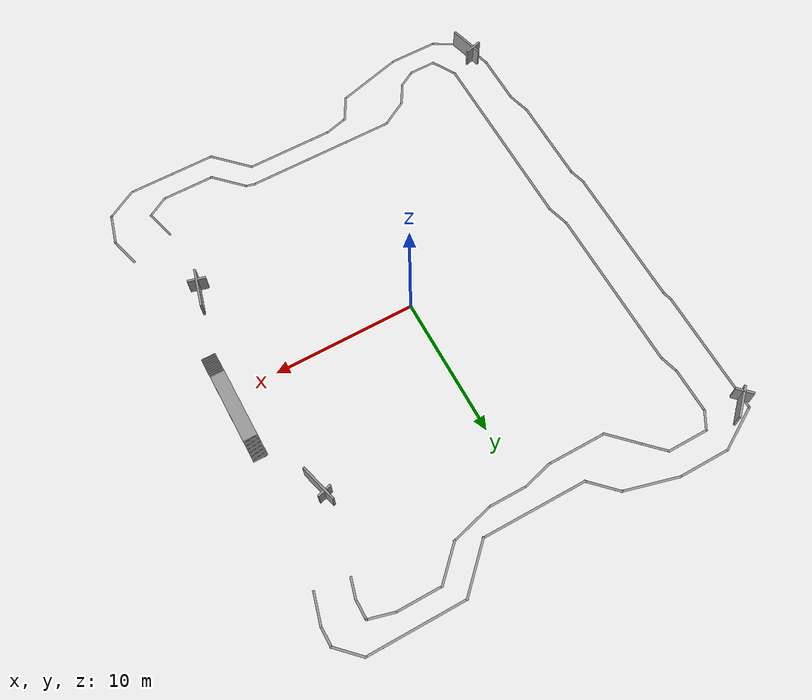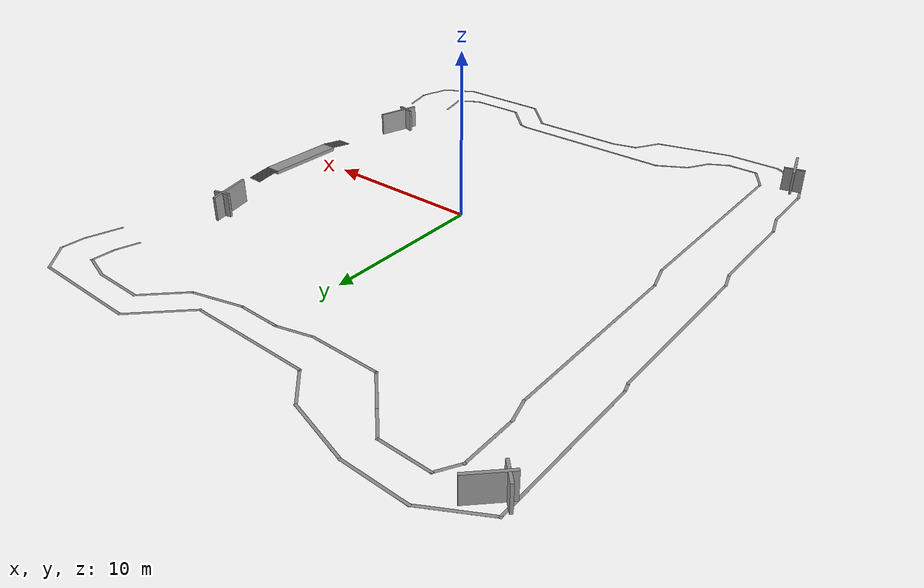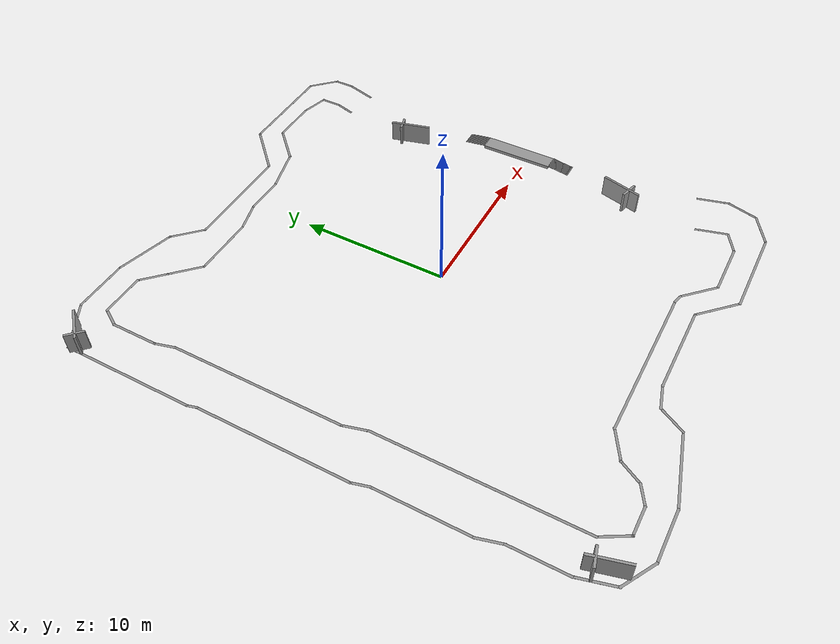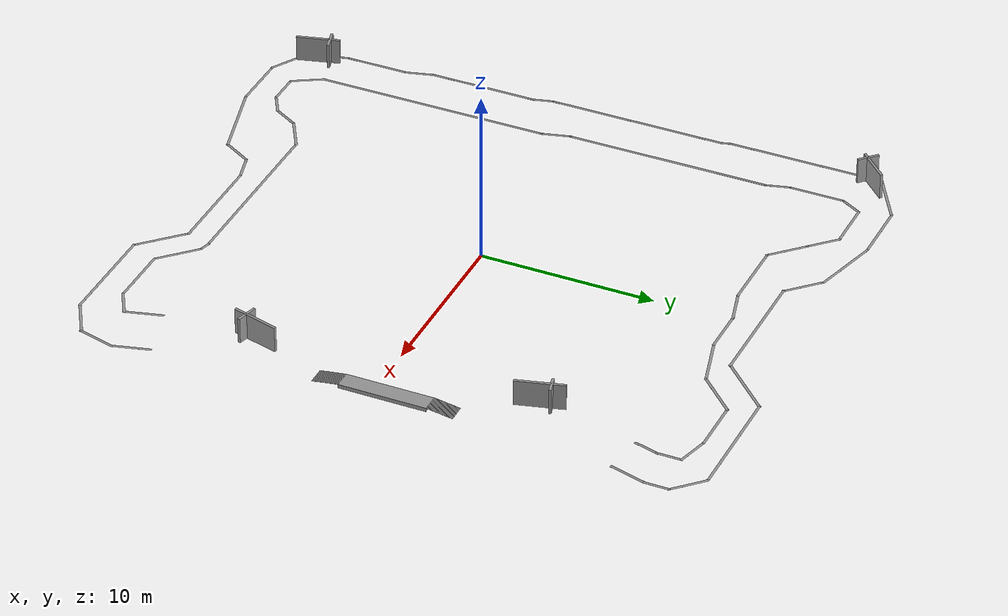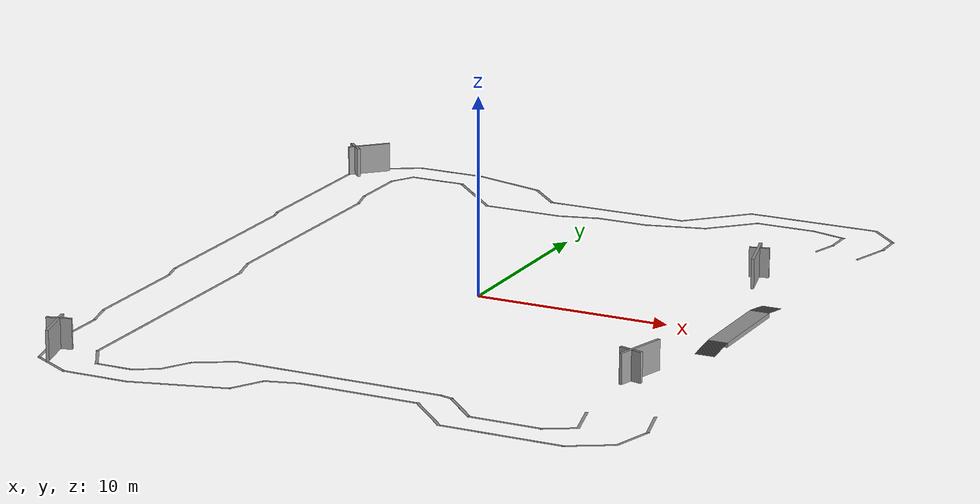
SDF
<?xml version='1.0'?>
<sdf version='1.7'>
  <model name='Course2023'>
    <pose>-0.154528 0.080991 0 0 -0 0</pose>
    <link name='Stairs_11'>
      <visual name='Stairs_11_Visual_0'>
        <pose>13.5343 -3.32779 0.00375 0 0 -3.14159</pose>
        <geometry>
          <box>
            <size>1 0.05 0.0075</size>
          </box>
        </geometry>
        <material>
          <script>
            <uri>file://media/materials/scripts/gazebo.material</uri>
            <name>Gazebo/Grey</name>
          </script>
          <ambient>1 1 1 1</ambient>
        </material>
        <meta>
          <layer>0</layer>
        </meta>
      </visual>
      <collision name='Stairs_11_Collision_0'>
        <geometry>
          <box>
            <size>1 0.05 0.0075</size>
          </box>
        </geometry>
        <pose>13.5343 -3.32779 0.00375 0 0 -3.14159</pose>
      </collision>
      <visual name='Stairs_11_Visual_1'>
        <pose>13.5343 -3.27779 0.01125 0 0 -3.14159</pose>
        <geometry>
          <box>
            <size>1 0.05 0.0075</size>
          </box>
        </geometry>
        <material>
          <script>
            <uri>file://media/materials/scripts/gazebo.material</uri>
            <name>Gazebo/Grey</name>
          </script>
          <ambient>1 1 1 1</ambient>
        </material>
        <meta>
          <layer>0</layer>
        </meta>
      </visual>
      <collision name='Stairs_11_Collision_1'>
        <geometry>
          <box>
            <size>1 0.05 0.0075</size>
          </box>
        </geometry>
        <pose>13.5343 -3.27779 0.01125 0 0 -3.14159</pose>
      </collision>
      <visual name='Stairs_11_Visual_2'>
        <pose>13.5343 -3.22779 0.01875 0 0 -3.14159</pose>
        <geometry>
          <box>
            <size>1 0.05 0.0075</size>
          </box>
        </geometry>
        <material>
          <script>
            <uri>file://media/materials/scripts/gazebo.material</uri>
            <name>Gazebo/Grey</name>
          </script>
          <ambient>1 1 1 1</ambient>
        </material>
        <meta>
          <layer>0</layer>
        </meta>
      </visual>
      <collision name='Stairs_11_Collision_2'>
        <geometry>
          <box>
            <size>1 0.05 0.0075</size>
          </box>
        </geometry>
        <pose>13.5343 -3.22779 0.01875 0 0 -3.14159</pose>
      </collision>
      <visual name='Stairs_11_Visual_3'>
        <pose>13.5343 -3.17779 0.02625 0 0 -3.14159</pose>
        <geometry>
          <box>
            <size>1 0.05 0.0075</size>
          </box>
        </geometry>
        <material>
          <script>
            <uri>file://media/materials/scripts/gazebo.material</uri>
            <name>Gazebo/Grey</name>
          </script>
          <ambient>1 1 1 1</ambient>
        </material>
        <meta>
          <layer>0</layer>
        </meta>
      </visual>
      <collision name='Stairs_11_Collision_3'>
        <geometry>
          <box>
            <size>1 0.05 0.0075</size>
          </box>
        </geometry>
        <pose>13.5343 -3.17779 0.02625 0 0 -3.14159</pose>
      </collision>
      <visual name='Stairs_11_Visual_4'>
        <pose>13.5343 -3.12779 0.03375 0 0 -3.14159</pose>
        <geometry>
          <box>
            <size>1 0.05 0.0075</size>
          </box>
        </geometry>
        <material>
          <script>
            <uri>file://media/materials/scripts/gazebo.material</uri>
            <name>Gazebo/Grey</name>
          </script>
          <ambient>1 1 1 1</ambient>
        </material>
        <meta>
          <layer>0</layer>
        </meta>
      </visual>
      <collision name='Stairs_11_Collision_4'>
        <geometry>
          <box>
            <size>1 0.05 0.0075</size>
          </box>
        </geometry>
        <pose>13.5343 -3.12779 0.03375 0 0 -3.14159</pose>
      </collision>
      <visual name='Stairs_11_Visual_5'>
        <pose>13.5343 -3.07779 0.04125 0 0 -3.14159</pose>
        <geometry>
          <box>
            <size>1 0.05 0.0075</size>
          </box>
        </geometry>
        <material>
          <script>
            <uri>file://media/materials/scripts/gazebo.material</uri>
            <name>Gazebo/Grey</name>
          </script>
          <ambient>1 1 1 1</ambient>
        </material>
        <meta>
          <layer>0</layer>
        </meta>
      </visual>
      <collision name='Stairs_11_Collision_5'>
        <geometry>
          <box>
            <size>1 0.05 0.0075</size>
          </box>
        </geometry>
        <pose>13.5343 -3.07779 0.04125 0 0 -3.14159</pose>
      </collision>
      <visual name='Stairs_11_Visual_6'>
        <pose>13.5343 -3.02779 0.04875 0 0 -3.14159</pose>
        <geometry>
          <box>
            <size>1 0.05 0.0075</size>
          </box>
        </geometry>
        <material>
          <script>
            <uri>file://media/materials/scripts/gazebo.material</uri>
            <name>Gazebo/Grey</name>
          </script>
          <ambient>1 1 1 1</ambient>
        </material>
        <meta>
          <layer>0</layer>
        </meta>
      </visual>
      <collision name='Stairs_11_Collision_6'>
        <geometry>
          <box>
            <size>1 0.05 0.0075</size>
          </box>
        </geometry>
        <pose>13.5343 -3.02779 0.04875 0 0 -3.14159</pose>
      </collision>
      <visual name='Stairs_11_Visual_7'>
        <pose>13.5343 -2.97779 0.05625 0 0 -3.14159</pose>
        <geometry>
          <box>
            <size>1 0.05 0.0075</size>
          </box>
        </geometry>
        <material>
          <script>
            <uri>file://media/materials/scripts/gazebo.material</uri>
            <name>Gazebo/Grey</name>
          </script>
          <ambient>1 1 1 1</ambient>
        </material>
        <meta>
          <layer>0</layer>
        </meta>
      </visual>
      <collision name='Stairs_11_Collision_7'>
        <geometry>
          <box>
            <size>1 0.05 0.0075</size>
          </box>
        </geometry>
        <pose>13.5343 -2.97779 0.05625 0 0 -3.14159</pose>
      </collision>
      <visual name='Stairs_11_Visual_8'>
        <pose>13.5343 -2.92779 0.06375 0 0 -3.14159</pose>
        <geometry>
          <box>
            <size>1 0.05 0.0075</size>
          </box>
        </geometry>
        <material>
          <script>
            <uri>file://media/materials/scripts/gazebo.material</uri>
            <name>Gazebo/Grey</name>
          </script>
          <ambient>1 1 1 1</ambient>
        </material>
        <meta>
          <layer>0</layer>
        </meta>
      </visual>
      <collision name='Stairs_11_Collision_8'>
        <geometry>
          <box>
            <size>1 0.05 0.0075</size>
          </box>
        </geometry>
        <pose>13.5343 -2.92779 0.06375 0 0 -3.14159</pose>
      </collision>
      <visual name='Stairs_11_Visual_9'>
        <pose>13.5343 -2.87779 0.07125 0 0 -3.14159</pose>
        <geometry>
          <box>
            <size>1 0.05 0.0075</size>
          </box>
        </geometry>
        <material>
          <script>
            <uri>file://media/materials/scripts/gazebo.material</uri>
            <name>Gazebo/Grey</name>
          </script>
          <ambient>1 1 1 1</ambient>
        </material>
        <meta>
          <layer>0</layer>
        </meta>
      </visual>
      <collision name='Stairs_11_Collision_9'>
        <geometry>
          <box>
            <size>1 0.05 0.0075</size>
          </box>
        </geometry>
        <pose>13.5343 -2.87779 0.07125 0 0 -3.14159</pose>
      </collision>
      <visual name='Stairs_11_Visual_10'>
        <pose>13.5343 -2.82779 0.07875 0 0 -3.14159</pose>
        <geometry>
          <box>
            <size>1 0.05 0.0075</size>
          </box>
        </geometry>
        <material>
          <script>
            <uri>file://media/materials/scripts/gazebo.material</uri>
            <name>Gazebo/Grey</name>
          </script>
          <ambient>1 1 1 1</ambient>
        </material>
        <meta>
          <layer>0</layer>
        </meta>
      </visual>
      <collision name='Stairs_11_Collision_10'>
        <geometry>
          <box>
            <size>1 0.05 0.0075</size>
          </box>
        </geometry>
        <pose>13.5343 -2.82779 0.07875 0 0 -3.14159</pose>
      </collision>
      <visual name='Stairs_11_Visual_11'>
        <pose>13.5343 -2.77779 0.08625 0 0 -3.14159</pose>
        <geometry>
          <box>
            <size>1 0.05 0.0075</size>
          </box>
        </geometry>
        <material>
          <script>
            <uri>file://media/materials/scripts/gazebo.material</uri>
            <name>Gazebo/Grey</name>
          </script>
          <ambient>1 1 1 1</ambient>
        </material>
        <meta>
          <layer>0</layer>
        </meta>
      </visual>
      <collision name='Stairs_11_Collision_11'>
        <geometry>
          <box>
            <size>1 0.05 0.0075</size>
          </box>
        </geometry>
        <pose>13.5343 -2.77779 0.08625 0 0 -3.14159</pose>
      </collision>
      <visual name='Stairs_11_Visual_12'>
        <pose>13.5343 -2.72779 0.09375 0 0 -3.14159</pose>
        <geometry>
          <box>
            <size>1 0.05 0.0075</size>
          </box>
        </geometry>
        <material>
          <script>
            <uri>file://media/materials/scripts/gazebo.material</uri>
            <name>Gazebo/Grey</name>
          </script>
          <ambient>1 1 1 1</ambient>
        </material>
        <meta>
          <layer>0</layer>
        </meta>
      </visual>
      <collision name='Stairs_11_Collision_12'>
        <geometry>
          <box>
            <size>1 0.05 0.0075</size>
          </box>
        </geometry>
        <pose>13.5343 -2.72779 0.09375 0 0 -3.14159</pose>
      </collision>
      <visual name='Stairs_11_Visual_13'>
        <pose>13.5343 -2.67779 0.10125 0 0 -3.14159</pose>
        <geometry>
          <box>
            <size>1 0.05 0.0075</size>
          </box>
        </geometry>
        <material>
          <script>
            <uri>file://media/materials/scripts/gazebo.material</uri>
            <name>Gazebo/Grey</name>
          </script>
          <ambient>1 1 1 1</ambient>
        </material>
        <meta>
          <layer>0</layer>
        </meta>
      </visual>
      <collision name='Stairs_11_Collision_13'>
        <geometry>
          <box>
            <size>1 0.05 0.0075</size>
          </box>
        </geometry>
        <pose>13.5343 -2.67779 0.10125 0 0 -3.14159</pose>
      </collision>
      <visual name='Stairs_11_Visual_14'>
        <pose>13.5343 -2.62779 0.10875 0 0 -3.14159</pose>
        <geometry>
          <box>
            <size>1 0.05 0.0075</size>
          </box>
        </geometry>
        <material>
          <script>
            <uri>file://media/materials/scripts/gazebo.material</uri>
            <name>Gazebo/Grey</name>
          </script>
          <ambient>1 1 1 1</ambient>
        </material>
        <meta>
          <layer>0</layer>
        </meta>
      </visual>
      <collision name='Stairs_11_Collision_14'>
        <geometry>
          <box>
            <size>1 0.05 0.0075</size>
          </box>
        </geometry>
        <pose>13.5343 -2.62779 0.10875 0 0 -3.14159</pose>
      </collision>
      <visual name='Stairs_11_Visual_15'>
        <pose>13.5343 -2.57779 0.11625 0 0 -3.14159</pose>
        <geometry>
          <box>
            <size>1 0.05 0.0075</size>
          </box>
        </geometry>
        <material>
          <script>
            <uri>file://media/materials/scripts/gazebo.material</uri>
            <name>Gazebo/Grey</name>
          </script>
          <ambient>1 1 1 1</ambient>
        </material>
        <meta>
          <layer>0</layer>
        </meta>
      </visual>
      <collision name='Stairs_11_Collision_15'>
        <geometry>
          <box>
            <size>1 0.05 0.0075</size>
          </box>
        </geometry>
        <pose>13.5343 -2.57779 0.11625 0 0 -3.14159</pose>
      </collision>
      <visual name='Stairs_11_Visual_16'>
        <pose>13.5343 -2.52779 0.12375 0 0 -3.14159</pose>
        <geometry>
          <box>
            <size>1 0.05 0.0075</size>
          </box>
        </geometry>
        <material>
          <script>
            <uri>file://media/materials/scripts/gazebo.material</uri>
            <name>Gazebo/Grey</name>
          </script>
          <ambient>1 1 1 1</ambient>
        </material>
        <meta>
          <layer>0</layer>
        </meta>
      </visual>
      <collision name='Stairs_11_Collision_16'>
        <geometry>
          <box>
            <size>1 0.05 0.0075</size>
          </box>
        </geometry>
        <pose>13.5343 -2.52779 0.12375 0 0 -3.14159</pose>
      </collision>
      <visual name='Stairs_11_Visual_17'>
        <pose>13.5343 -2.47779 0.13125 0 0 -3.14159</pose>
        <geometry>
          <box>
            <size>1 0.05 0.0075</size>
          </box>
        </geometry>
        <material>
          <script>
            <uri>file://media/materials/scripts/gazebo.material</uri>
            <name>Gazebo/Grey</name>
          </script>
          <ambient>1 1 1 1</ambient>
        </material>
        <meta>
          <layer>0</layer>
        </meta>
      </visual>
      <collision name='Stairs_11_Collision_17'>
        <geometry>
          <box>
            <size>1 0.05 0.0075</size>
          </box>
        </geometry>
        <pose>13.5343 -2.47779 0.13125 0 0 -3.14159</pose>
      </collision>
      <visual name='Stairs_11_Visual_18'>
        <pose>13.5343 -2.42779 0.13875 0 0 -3.14159</pose>
        <geometry>
          <box>
            <size>1 0.05 0.0075</size>
          </box>
        </geometry>
        <material>
          <script>
            <uri>file://media/materials/scripts/gazebo.material</uri>
            <name>Gazebo/Grey</name>
          </script>
          <ambient>1 1 1 1</ambient>
        </material>
        <meta>
          <layer>0</layer>
        </meta>
      </visual>
      <collision name='Stairs_11_Collision_18'>
        <geometry>
          <box>
            <size>1 0.05 0.0075</size>
          </box>
        </geometry>
        <pose>13.5343 -2.42779 0.13875 0 0 -3.14159</pose>
      </collision>
      <visual name='Stairs_11_Visual_19'>
        <pose>13.5343 -2.37779 0.14625 0 0 -3.14159</pose>
        <geometry>
          <box>
            <size>1 0.05 0.0075</size>
          </box>
        </geometry>
        <material>
          <script>
            <uri>file://media/materials/scripts/gazebo.material</uri>
            <name>Gazebo/Grey</name>
          </script>
          <ambient>1 1 1 1</ambient>
        </material>
        <meta>
          <layer>0</layer>
        </meta>
      </visual>
      <collision name='Stairs_11_Collision_19'>
        <geometry>
          <box>
            <size>1 0.05 0.0075</size>
          </box>
        </geometry>
        <pose>13.5343 -2.37779 0.14625 0 0 -3.14159</pose>
      </collision>
      <visual name='Stairs_11_Visual_20'>
        <pose>13.5343 -2.32779 0.15375 0 0 -3.14159</pose>
        <geometry>
          <box>
            <size>1 0.05 0.0075</size>
          </box>
        </geometry>
        <material>
          <script>
            <uri>file://media/materials/scripts/gazebo.material</uri>
            <name>Gazebo/Grey</name>
          </script>
          <ambient>1 1 1 1</ambient>
        </material>
        <meta>
          <layer>0</layer>
        </meta>
      </visual>
      <collision name='Stairs_11_Collision_20'>
        <geometry>
          <box>
            <size>1 0.05 0.0075</size>
          </box>
        </geometry>
        <pose>13.5343 -2.32779 0.15375 0 0 -3.14159</pose>
      </collision>
      <visual name='Stairs_11_Visual_21'>
        <pose>13.5343 -2.27779 0.16125 0 0 -3.14159</pose>
        <geometry>
          <box>
            <size>1 0.05 0.0075</size>
          </box>
        </geometry>
        <material>
          <script>
            <uri>file://media/materials/scripts/gazebo.material</uri>
            <name>Gazebo/Grey</name>
          </script>
          <ambient>1 1 1 1</ambient>
        </material>
        <meta>
          <layer>0</layer>
        </meta>
      </visual>
      <collision name='Stairs_11_Collision_21'>
        <geometry>
          <box>
            <size>1 0.05 0.0075</size>
          </box>
        </geometry>
        <pose>13.5343 -2.27779 0.16125 0 0 -3.14159</pose>
      </collision>
      <visual name='Stairs_11_Visual_22'>
        <pose>13.5343 -2.22779 0.16875 0 0 -3.14159</pose>
        <geometry>
          <box>
            <size>1 0.05 0.0075</size>
          </box>
        </geometry>
        <material>
          <script>
            <uri>file://media/materials/scripts/gazebo.material</uri>
            <name>Gazebo/Grey</name>
          </script>
          <ambient>1 1 1 1</ambient>
        </material>
        <meta>
          <layer>0</layer>
        </meta>
      </visual>
      <collision name='Stairs_11_Collision_22'>
        <geometry>
          <box>
            <size>1 0.05 0.0075</size>
          </box>
        </geometry>
        <pose>13.5343 -2.22779 0.16875 0 0 -3.14159</pose>
      </collision>
      <visual name='Stairs_11_Visual_23'>
        <pose>13.5343 -2.17779 0.17625 0 0 -3.14159</pose>
        <geometry>
          <box>
            <size>1 0.05 0.0075</size>
          </box>
        </geometry>
        <material>
          <script>
            <uri>file://media/materials/scripts/gazebo.material</uri>
            <name>Gazebo/Grey</name>
          </script>
          <ambient>1 1 1 1</ambient>
        </material>
        <meta>
          <layer>0</layer>
        </meta>
      </visual>
      <collision name='Stairs_11_Collision_23'>
        <geometry>
          <box>
            <size>1 0.05 0.0075</size>
          </box>
        </geometry>
        <pose>13.5343 -2.17779 0.17625 0 0 -3.14159</pose>
      </collision>
      <visual name='Stairs_11_Visual_24'>
        <pose>13.5343 -2.12779 0.18375 0 0 -3.14159</pose>
        <geometry>
          <box>
            <size>1 0.05 0.0075</size>
          </box>
        </geometry>
        <material>
          <script>
            <uri>file://media/materials/scripts/gazebo.material</uri>
            <name>Gazebo/Grey</name>
          </script>
          <ambient>1 1 1 1</ambient>
        </material>
        <meta>
          <layer>0</layer>
        </meta>
      </visual>
      <collision name='Stairs_11_Collision_24'>
        <geometry>
          <box>
            <size>1 0.05 0.0075</size>
          </box>
        </geometry>
        <pose>13.5343 -2.12779 0.18375 0 0 -3.14159</pose>
      </collision>
      <visual name='Stairs_11_Visual_25'>
        <pose>13.5343 -2.07779 0.19125 0 0 -3.14159</pose>
        <geometry>
          <box>
            <size>1 0.05 0.0075</size>
          </box>
        </geometry>
        <material>
          <script>
            <uri>file://media/materials/scripts/gazebo.material</uri>
            <name>Gazebo/Grey</name>
          </script>
          <ambient>1 1 1 1</ambient>
        </material>
        <meta>
          <layer>0</layer>
        </meta>
      </visual>
      <collision name='Stairs_11_Collision_25'>
        <geometry>
          <box>
            <size>1 0.05 0.0075</size>
          </box>
        </geometry>
        <pose>13.5343 -2.07779 0.19125 0 0 -3.14159</pose>
      </collision>
      <visual name='Stairs_11_Visual_26'>
        <pose>13.5343 -2.02779 0.19875 0 0 -3.14159</pose>
        <geometry>
          <box>
            <size>1 0.05 0.0075</size>
          </box>
        </geometry>
        <material>
          <script>
            <uri>file://media/materials/scripts/gazebo.material</uri>
            <name>Gazebo/Grey</name>
          </script>
          <ambient>1 1 1 1</ambient>
        </material>
        <meta>
          <layer>0</layer>
        </meta>
      </visual>
      <collision name='Stairs_11_Collision_26'>
        <geometry>
          <box>
            <size>1 0.05 0.0075</size>
          </box>
        </geometry>
        <pose>13.5343 -2.02779 0.19875 0 0 -3.14159</pose>
      </collision>
      <visual name='Stairs_11_Visual_27'>
        <pose>13.5343 -1.97779 0.20625 0 0 -3.14159</pose>
        <geometry>
          <box>
            <size>1 0.05 0.0075</size>
          </box>
        </geometry>
        <material>
          <script>
            <uri>file://media/materials/scripts/gazebo.material</uri>
            <name>Gazebo/Grey</name>
          </script>
          <ambient>1 1 1 1</ambient>
        </material>
        <meta>
          <layer>0</layer>
        </meta>
      </visual>
      <collision name='Stairs_11_Collision_27'>
        <geometry>
          <box>
            <size>1 0.05 0.0075</size>
          </box>
        </geometry>
        <pose>13.5343 -1.97779 0.20625 0 0 -3.14159</pose>
      </collision>
      <visual name='Stairs_11_Visual_28'>
        <pose>13.5343 -1.92779 0.21375 0 0 -3.14159</pose>
        <geometry>
          <box>
            <size>1 0.05 0.0075</size>
          </box>
        </geometry>
        <material>
          <script>
            <uri>file://media/materials/scripts/gazebo.material</uri>
            <name>Gazebo/Grey</name>
          </script>
          <ambient>1 1 1 1</ambient>
        </material>
        <meta>
          <layer>0</layer>
        </meta>
      </visual>
      <collision name='Stairs_11_Collision_28'>
        <geometry>
          <box>
            <size>1 0.05 0.0075</size>
          </box>
        </geometry>
        <pose>13.5343 -1.92779 0.21375 0 0 -3.14159</pose>
      </collision>
      <visual name='Stairs_11_Visual_29'>
        <pose>13.5343 -1.87779 0.22125 0 0 -3.14159</pose>
        <geometry>
          <box>
            <size>1 0.05 0.0075</size>
          </box>
        </geometry>
        <material>
          <script>
            <uri>file://media/materials/scripts/gazebo.material</uri>
            <name>Gazebo/Grey</name>
          </script>
          <ambient>1 1 1 1</ambient>
        </material>
        <meta>
          <layer>0</layer>
        </meta>
      </visual>
      <collision name='Stairs_11_Collision_29'>
        <geometry>
          <box>
            <size>1 0.05 0.0075</size>
          </box>
        </geometry>
        <pose>13.5343 -1.87779 0.22125 0 0 -3.14159</pose>
      </collision>
    </link>
    <link name='Stairs_12'>
      <visual name='Stairs_12_Visual_0'>
        <pose>13.5207 4.63123 0.00375 0 -0 0</pose>
        <geometry>
          <box>
            <size>1 0.05 0.0075</size>
          </box>
        </geometry>
        <material>
          <script>
            <uri>file://media/materials/scripts/gazebo.material</uri>
            <name>Gazebo/Grey</name>
          </script>
          <ambient>1 1 1 1</ambient>
        </material>
        <meta>
          <layer>0</layer>
        </meta>
      </visual>
      <collision name='Stairs_12_Collision_0'>
        <geometry>
          <box>
            <size>1 0.05 0.0075</size>
          </box>
        </geometry>
        <pose>13.5207 4.63123 0.00375 0 -0 0</pose>
      </collision>
      <visual name='Stairs_12_Visual_1'>
        <pose>13.5207 4.58123 0.01125 0 -0 0</pose>
        <geometry>
          <box>
            <size>1 0.05 0.0075</size>
          </box>
        </geometry>
        <material>
          <script>
            <uri>file://media/materials/scripts/gazebo.material</uri>
            <name>Gazebo/Grey</name>
          </script>
          <ambient>1 1 1 1</ambient>
        </material>
        <meta>
          <layer>0</layer>
        </meta>
      </visual>
      <collision name='Stairs_12_Collision_1'>
        <geometry>
          <box>
            <size>1 0.05 0.0075</size>
          </box>
        </geometry>
        <pose>13.5207 4.58123 0.01125 0 -0 0</pose>
      </collision>
      <visual name='Stairs_12_Visual_2'>
        <pose>13.5207 4.53123 0.01875 0 -0 0</pose>
        <geometry>
          <box>
            <size>1 0.05 0.0075</size>
          </box>
        </geometry>
        <material>
          <script>
            <uri>file://media/materials/scripts/gazebo.material</uri>
            <name>Gazebo/Grey</name>
          </script>
          <ambient>1 1 1 1</ambient>
        </material>
        <meta>
          <layer>0</layer>
        </meta>
      </visual>
      <collision name='Stairs_12_Collision_2'>
        <geometry>
          <box>
            <size>1 0.05 0.0075</size>
          </box>
        </geometry>
        <pose>13.5207 4.53123 0.01875 0 -0 0</pose>
      </collision>
      <visual name='Stairs_12_Visual_3'>
        <pose>13.5207 4.48123 0.02625 0 -0 0</pose>
        <geometry>
          <box>
            <size>1 0.05 0.0075</size>
          </box>
        </geometry>
        <material>
          <script>
            <uri>file://media/materials/scripts/gazebo.material</uri>
            <name>Gazebo/Grey</name>
          </script>
          <ambient>1 1 1 1</ambient>
        </material>
        <meta>
          <layer>0</layer>
        </meta>
      </visual>
      <collision name='Stairs_12_Collision_3'>
        <geometry>
          <box>
            <size>1 0.05 0.0075</size>
          </box>
        </geometry>
        <pose>13.5207 4.48123 0.02625 0 -0 0</pose>
      </collision>
      <visual name='Stairs_12_Visual_4'>
        <pose>13.5207 4.43123 0.03375 0 -0 0</pose>
        <geometry>
          <box>
            <size>1 0.05 0.0075</size>
          </box>
        </geometry>
        <material>
          <script>
            <uri>file://media/materials/scripts/gazebo.material</uri>
            <name>Gazebo/Grey</name>
          </script>
          <ambient>1 1 1 1</ambient>
        </material>
        <meta>
          <layer>0</layer>
        </meta>
      </visual>
      <collision name='Stairs_12_Collision_4'>
        <geometry>
          <box>
            <size>1 0.05 0.0075</size>
          </box>
        </geometry>
        <pose>13.5207 4.43123 0.03375 0 -0 0</pose>
      </collision>
      <visual name='Stairs_12_Visual_5'>
        <pose>13.5207 4.38123 0.04125 0 -0 0</pose>
        <geometry>
          <box>
            <size>1 0.05 0.0075</size>
          </box>
        </geometry>
        <material>
          <script>
            <uri>file://media/materials/scripts/gazebo.material</uri>
            <name>Gazebo/Grey</name>
          </script>
          <ambient>1 1 1 1</ambient>
        </material>
        <meta>
          <layer>0</layer>
        </meta>
      </visual>
      <collision name='Stairs_12_Collision_5'>
        <geometry>
          <box>
            <size>1 0.05 0.0075</size>
          </box>
        </geometry>
        <pose>13.5207 4.38123 0.04125 0 -0 0</pose>
      </collision>
      <visual name='Stairs_12_Visual_6'>
        <pose>13.5207 4.33123 0.04875 0 -0 0</pose>
        <geometry>
          <box>
            <size>1 0.05 0.0075</size>
          </box>
        </geometry>
        <material>
          <script>
            <uri>file://media/materials/scripts/gazebo.material</uri>
            <name>Gazebo/Grey</name>
          </script>
          <ambient>1 1 1 1</ambient>
        </material>
        <meta>
          <layer>0</layer>
        </meta>
      </visual>
      <collision name='Stairs_12_Collision_6'>
        <geometry>
          <box>
            <size>1 0.05 0.0075</size>
          </box>
        </geometry>
        <pose>13.5207 4.33123 0.04875 0 -0 0</pose>
      </collision>
      <visual name='Stairs_12_Visual_7'>
        <pose>13.5207 4.28123 0.05625 0 -0 0</pose>
        <geometry>
          <box>
            <size>1 0.05 0.0075</size>
          </box>
        </geometry>
        <material>
          <script>
            <uri>file://media/materials/scripts/gazebo.material</uri>
            <name>Gazebo/Grey</name>
          </script>
          <ambient>1 1 1 1</ambient>
        </material>
        <meta>
          <layer>0</layer>
        </meta>
      </visual>
      <collision name='Stairs_12_Collision_7'>
        <geometry>
          <box>
            <size>1 0.05 0.0075</size>
          </box>
        </geometry>
        <pose>13.5207 4.28123 0.05625 0 -0 0</pose>
      </collision>
      <visual name='Stairs_12_Visual_8'>
        <pose>13.5207 4.23123 0.06375 0 -0 0</pose>
        <geometry>
          <box>
            <size>1 0.05 0.0075</size>
          </box>
        </geometry>
        <material>
          <script>
            <uri>file://media/materials/scripts/gazebo.material</uri>
            <name>Gazebo/Grey</name>
          </script>
          <ambient>1 1 1 1</ambient>
        </material>
        <meta>
          <layer>0</layer>
        </meta>
      </visual>
      <collision name='Stairs_12_Collision_8'>
        <geometry>
          <box>
            <size>1 0.05 0.0075</size>
          </box>
        </geometry>
        <pose>13.5207 4.23123 0.06375 0 -0 0</pose>
      </collision>
      <visual name='Stairs_12_Visual_9'>
        <pose>13.5207 4.18123 0.07125 0 -0 0</pose>
        <geometry>
          <box>
            <size>1 0.05 0.0075</size>
          </box>
        </geometry>
        <material>
          <script>
            <uri>file://media/materials/scripts/gazebo.material</uri>
            <name>Gazebo/Grey</name>
          </script>
          <ambient>1 1 1 1</ambient>
        </material>
        <meta>
          <layer>0</layer>
        </meta>
      </visual>
      <collision name='Stairs_12_Collision_9'>
        <geometry>
          <box>
            <size>1 0.05 0.0075</size>
          </box>
        </geometry>
        <pose>13.5207 4.18123 0.07125 0 -0 0</pose>
      </collision>
      <visual name='Stairs_12_Visual_10'>
        <pose>13.5207 4.13123 0.07875 0 -0 0</pose>
        <geometry>
          <box>
            <size>1 0.05 0.0075</size>
          </box>
        </geometry>
        <material>
          <script>
            <uri>file://media/materials/scripts/gazebo.material</uri>
            <name>Gazebo/Grey</name>
          </script>
          <ambient>1 1 1 1</ambient>
        </material>
        <meta>
          <layer>0</layer>
        </meta>
      </visual>
      <collision name='Stairs_12_Collision_10'>
        <geometry>
          <box>
            <size>1 0.05 0.0075</size>
          </box>
        </geometry>
        <pose>13.5207 4.13123 0.07875 0 -0 0</pose>
      </collision>
      <visual name='Stairs_12_Visual_11'>
        <pose>13.5207 4.08123 0.08625 0 -0 0</pose>
        <geometry>
          <box>
            <size>1 0.05 0.0075</size>
          </box>
        </geometry>
        <material>
          <script>
            <uri>file://media/materials/scripts/gazebo.material</uri>
            <name>Gazebo/Grey</name>
          </script>
          <ambient>1 1 1 1</ambient>
        </material>
        <meta>
          <layer>0</layer>
        </meta>
      </visual>
      <collision name='Stairs_12_Collision_11'>
        <geometry>
          <box>
            <size>1 0.05 0.0075</size>
          </box>
        </geometry>
        <pose>13.5207 4.08123 0.08625 0 -0 0</pose>
      </collision>
      <visual name='Stairs_12_Visual_12'>
        <pose>13.5207 4.03123 0.09375 0 -0 0</pose>
        <geometry>
          <box>
            <size>1 0.05 0.0075</size>
          </box>
        </geometry>
        <material>
          <script>
            <uri>file://media/materials/scripts/gazebo.material</uri>
            <name>Gazebo/Grey</name>
          </script>
          <ambient>1 1 1 1</ambient>
        </material>
        <meta>
          <layer>0</layer>
        </meta>
      </visual>
      <collision name='Stairs_12_Collision_12'>
        <geometry>
          <box>
            <size>1 0.05 0.0075</size>
          </box>
        </geometry>
        <pose>13.5207 4.03123 0.09375 0 -0 0</pose>
      </collision>
      <visual name='Stairs_12_Visual_13'>
        <pose>13.5207 3.98123 0.10125 0 -0 0</pose>
        <geometry>
          <box>
            <size>1 0.05 0.0075</size>
          </box>
        </geometry>
        <material>
          <script>
            <uri>file://media/materials/scripts/gazebo.material</uri>
            <name>Gazebo/Grey</name>
          </script>
          <ambient>1 1 1 1</ambient>
        </material>
        <meta>
          <layer>0</layer>
        </meta>
      </visual>
      <collision name='Stairs_12_Collision_13'>
        <geometry>
          <box>
            <size>1 0.05 0.0075</size>
          </box>
        </geometry>
        <pose>13.5207 3.98123 0.10125 0 -0 0</pose>
      </collision>
      <visual name='Stairs_12_Visual_14'>
        <pose>13.5207 3.93123 0.10875 0 -0 0</pose>
        <geometry>
          <box>
            <size>1 0.05 0.0075</size>
          </box>
        </geometry>
        <material>
          <script>
            <uri>file://media/materials/scripts/gazebo.material</uri>
            <name>Gazebo/Grey</name>
          </script>
          <ambient>1 1 1 1</ambient>
        </material>
        <meta>
          <layer>0</layer>
        </meta>
      </visual>
      <collision name='Stairs_12_Collision_14'>
        <geometry>
          <box>
            <size>1 0.05 0.0075</size>
          </box>
        </geometry>
        <pose>13.5207 3.93123 0.10875 0 -0 0</pose>
      </collision>
      <visual name='Stairs_12_Visual_15'>
        <pose>13.5207 3.88123 0.11625 0 -0 0</pose>
        <geometry>
          <box>
            <size>1 0.05 0.0075</size>
          </box>
        </geometry>
        <material>
          <script>
            <uri>file://media/materials/scripts/gazebo.material</uri>
            <name>Gazebo/Grey</name>
          </script>
          <ambient>1 1 1 1</ambient>
        </material>
        <meta>
          <layer>0</layer>
        </meta>
      </visual>
      <collision name='Stairs_12_Collision_15'>
        <geometry>
          <box>
            <size>1 0.05 0.0075</size>
          </box>
        </geometry>
        <pose>13.5207 3.88123 0.11625 0 -0 0</pose>
      </collision>
      <visual name='Stairs_12_Visual_16'>
        <pose>13.5207 3.83123 0.12375 0 -0 0</pose>
        <geometry>
          <box>
            <size>1 0.05 0.0075</size>
          </box>
        </geometry>
        <material>
          <script>
            <uri>file://media/materials/scripts/gazebo.material</uri>
            <name>Gazebo/Grey</name>
          </script>
          <ambient>1 1 1 1</ambient>
        </material>
        <meta>
          <layer>0</layer>
        </meta>
      </visual>
      <collision name='Stairs_12_Collision_16'>
        <geometry>
          <box>
            <size>1 0.05 0.0075</size>
          </box>
        </geometry>
        <pose>13.5207 3.83123 0.12375 0 -0 0</pose>
      </collision>
      <visual name='Stairs_12_Visual_17'>
        <pose>13.5207 3.78123 0.13125 0 -0 0</pose>
        <geometry>
          <box>
            <size>1 0.05 0.0075</size>
          </box>
        </geometry>
        <material>
          <script>
            <uri>file://media/materials/scripts/gazebo.material</uri>
            <name>Gazebo/Grey</name>
          </script>
          <ambient>1 1 1 1</ambient>
        </material>
        <meta>
          <layer>0</layer>
        </meta>
      </visual>
      <collision name='Stairs_12_Collision_17'>
        <geometry>
          <box>
            <size>1 0.05 0.0075</size>
          </box>
        </geometry>
        <pose>13.5207 3.78123 0.13125 0 -0 0</pose>
      </collision>
      <visual name='Stairs_12_Visual_18'>
        <pose>13.5207 3.73123 0.13875 0 -0 0</pose>
        <geometry>
          <box>
            <size>1 0.05 0.0075</size>
          </box>
        </geometry>
        <material>
          <script>
            <uri>file://media/materials/scripts/gazebo.material</uri>
            <name>Gazebo/Grey</name>
          </script>
          <ambient>1 1 1 1</ambient>
        </material>
        <meta>
          <layer>0</layer>
        </meta>
      </visual>
      <collision name='Stairs_12_Collision_18'>
        <geometry>
          <box>
            <size>1 0.05 0.0075</size>
          </box>
        </geometry>
        <pose>13.5207 3.73123 0.13875 0 -0 0</pose>
      </collision>
      <visual name='Stairs_12_Visual_19'>
        <pose>13.5207 3.68123 0.14625 0 -0 0</pose>
        <geometry>
          <box>
            <size>1 0.05 0.0075</size>
          </box>
        </geometry>
        <material>
          <script>
            <uri>file://media/materials/scripts/gazebo.material</uri>
            <name>Gazebo/Grey</name>
          </script>
          <ambient>1 1 1 1</ambient>
        </material>
        <meta>
          <layer>0</layer>
        </meta>
      </visual>
      <collision name='Stairs_12_Collision_19'>
        <geometry>
          <box>
            <size>1 0.05 0.0075</size>
          </box>
        </geometry>
        <pose>13.5207 3.68123 0.14625 0 -0 0</pose>
      </collision>
      <visual name='Stairs_12_Visual_20'>
        <pose>13.5207 3.63123 0.15375 0 -0 0</pose>
        <geometry>
          <box>
            <size>1 0.05 0.0075</size>
          </box>
        </geometry>
        <material>
          <script>
            <uri>file://media/materials/scripts/gazebo.material</uri>
            <name>Gazebo/Grey</name>
          </script>
          <ambient>1 1 1 1</ambient>
        </material>
        <meta>
          <layer>0</layer>
        </meta>
      </visual>
      <collision name='Stairs_12_Collision_20'>
        <geometry>
          <box>
            <size>1 0.05 0.0075</size>
          </box>
        </geometry>
        <pose>13.5207 3.63123 0.15375 0 -0 0</pose>
      </collision>
      <visual name='Stairs_12_Visual_21'>
        <pose>13.5207 3.58123 0.16125 0 -0 0</pose>
        <geometry>
          <box>
            <size>1 0.05 0.0075</size>
          </box>
        </geometry>
        <material>
          <script>
            <uri>file://media/materials/scripts/gazebo.material</uri>
            <name>Gazebo/Grey</name>
          </script>
          <ambient>1 1 1 1</ambient>
        </material>
        <meta>
          <layer>0</layer>
        </meta>
      </visual>
      <collision name='Stairs_12_Collision_21'>
        <geometry>
          <box>
            <size>1 0.05 0.0075</size>
          </box>
        </geometry>
        <pose>13.5207 3.58123 0.16125 0 -0 0</pose>
      </collision>
      <visual name='Stairs_12_Visual_22'>
        <pose>13.5207 3.53123 0.16875 0 -0 0</pose>
        <geometry>
          <box>
            <size>1 0.05 0.0075</size>
          </box>
        </geometry>
        <material>
          <script>
            <uri>file://media/materials/scripts/gazebo.material</uri>
            <name>Gazebo/Grey</name>
          </script>
          <ambient>1 1 1 1</ambient>
        </material>
        <meta>
          <layer>0</layer>
        </meta>
      </visual>
      <collision name='Stairs_12_Collision_22'>
        <geometry>
          <box>
            <size>1 0.05 0.0075</size>
          </box>
        </geometry>
        <pose>13.5207 3.53123 0.16875 0 -0 0</pose>
      </collision>
      <visual name='Stairs_12_Visual_23'>
        <pose>13.5207 3.48123 0.17625 0 -0 0</pose>
        <geometry>
          <box>
            <size>1 0.05 0.0075</size>
          </box>
        </geometry>
        <material>
          <script>
            <uri>file://media/materials/scripts/gazebo.material</uri>
            <name>Gazebo/Grey</name>
          </script>
          <ambient>1 1 1 1</ambient>
        </material>
        <meta>
          <layer>0</layer>
        </meta>
      </visual>
      <collision name='Stairs_12_Collision_23'>
        <geometry>
          <box>
            <size>1 0.05 0.0075</size>
          </box>
        </geometry>
        <pose>13.5207 3.48123 0.17625 0 -0 0</pose>
      </collision>
      <visual name='Stairs_12_Visual_24'>
        <pose>13.5207 3.43123 0.18375 0 -0 0</pose>
        <geometry>
          <box>
            <size>1 0.05 0.0075</size>
          </box>
        </geometry>
        <material>
          <script>
            <uri>file://media/materials/scripts/gazebo.material</uri>
            <name>Gazebo/Grey</name>
          </script>
          <ambient>1 1 1 1</ambient>
        </material>
        <meta>
          <layer>0</layer>
        </meta>
      </visual>
      <collision name='Stairs_12_Collision_24'>
        <geometry>
          <box>
            <size>1 0.05 0.0075</size>
          </box>
        </geometry>
        <pose>13.5207 3.43123 0.18375 0 -0 0</pose>
      </collision>
      <visual name='Stairs_12_Visual_25'>
        <pose>13.5207 3.38123 0.19125 0 -0 0</pose>
        <geometry>
          <box>
            <size>1 0.05 0.0075</size>
          </box>
        </geometry>
        <material>
          <script>
            <uri>file://media/materials/scripts/gazebo.material</uri>
            <name>Gazebo/Grey</name>
          </script>
          <ambient>1 1 1 1</ambient>
        </material>
        <meta>
          <layer>0</layer>
        </meta>
      </visual>
      <collision name='Stairs_12_Collision_25'>
        <geometry>
          <box>
            <size>1 0.05 0.0075</size>
          </box>
        </geometry>
        <pose>13.5207 3.38123 0.19125 0 -0 0</pose>
      </collision>
      <visual name='Stairs_12_Visual_26'>
        <pose>13.5207 3.33123 0.19875 0 -0 0</pose>
        <geometry>
          <box>
            <size>1 0.05 0.0075</size>
          </box>
        </geometry>
        <material>
          <script>
            <uri>file://media/materials/scripts/gazebo.material</uri>
            <name>Gazebo/Grey</name>
          </script>
          <ambient>1 1 1 1</ambient>
        </material>
        <meta>
          <layer>0</layer>
        </meta>
      </visual>
      <collision name='Stairs_12_Collision_26'>
        <geometry>
          <box>
            <size>1 0.05 0.0075</size>
          </box>
        </geometry>
        <pose>13.5207 3.33123 0.19875 0 -0 0</pose>
      </collision>
      <visual name='Stairs_12_Visual_27'>
        <pose>13.5207 3.28123 0.20625 0 -0 0</pose>
        <geometry>
          <box>
            <size>1 0.05 0.0075</size>
          </box>
        </geometry>
        <material>
          <script>
            <uri>file://media/materials/scripts/gazebo.material</uri>
            <name>Gazebo/Grey</name>
          </script>
          <ambient>1 1 1 1</ambient>
        </material>
        <meta>
          <layer>0</layer>
        </meta>
      </visual>
      <collision name='Stairs_12_Collision_27'>
        <geometry>
          <box>
            <size>1 0.05 0.0075</size>
          </box>
        </geometry>
        <pose>13.5207 3.28123 0.20625 0 -0 0</pose>
      </collision>
      <visual name='Stairs_12_Visual_28'>
        <pose>13.5207 3.23123 0.21375 0 -0 0</pose>
        <geometry>
          <box>
            <size>1 0.05 0.0075</size>
          </box>
        </geometry>
        <material>
          <script>
            <uri>file://media/materials/scripts/gazebo.material</uri>
            <name>Gazebo/Grey</name>
          </script>
          <ambient>1 1 1 1</ambient>
        </material>
        <meta>
          <layer>0</layer>
        </meta>
      </visual>
      <collision name='Stairs_12_Collision_28'>
        <geometry>
          <box>
            <size>1 0.05 0.0075</size>
          </box>
        </geometry>
        <pose>13.5207 3.23123 0.21375 0 -0 0</pose>
      </collision>
      <visual name='Stairs_12_Visual_29'>
        <pose>13.5207 3.18123 0.22125 0 -0 0</pose>
        <geometry>
          <box>
            <size>1 0.05 0.0075</size>
          </box>
        </geometry>
        <material>
          <script>
            <uri>file://media/materials/scripts/gazebo.material</uri>
            <name>Gazebo/Grey</name>
          </script>
          <ambient>1 1 1 1</ambient>
        </material>
        <meta>
          <layer>0</layer>
        </meta>
      </visual>
      <collision name='Stairs_12_Collision_29'>
        <geometry>
          <box>
            <size>1 0.05 0.0075</size>
          </box>
        </geometry>
        <pose>13.5207 3.18123 0.22125 0 -0 0</pose>
      </collision>
    </link>
    <link name='Stairs_8'>
      <visual name='Stairs_8_Visual_0'>
        <pose>13.5258 0.655595 0.1125 0 -0 0</pose>
        <geometry>
          <box>
            <size>1 5 0.225</size>
          </box>
        </geometry>
        <material>
          <script>
            <uri>file://media/materials/scripts/gazebo.material</uri>
            <name>Gazebo/Grey</name>
          </script>
          <ambient>1 1 1 1</ambient>
        </material>
        <meta>
          <layer>0</layer>
        </meta>
      </visual>
      <collision name='Stairs_8_Collision_0'>
        <geometry>
          <box>
            <size>1 5 0.225</size>
          </box>
        </geometry>
        <pose>13.5258 0.655595 0.1125 0 -0 0</pose>
      </collision>
    </link>
    <link name='Wall_10'>
      <collision name='Wall_10_Collision'>
        <geometry>
          <box>
            <size>3.75 0.15 0.001</size>
          </box>
        </geometry>
        <pose>0 0 0.0005 0 -0 0</pose>
      </collision>
      <visual name='Wall_10_Visual'>
        <pose>0 0 0.0005 0 -0 0</pose>
        <geometry>
          <box>
            <size>3.75 0.15 0.001</size>
          </box>
        </geometry>
        <material>
          <script>
            <uri>file://media/materials/scripts/gazebo.material</uri>
            <name>Gazebo/Grey</name>
          </script>
          <ambient>1 1 1 1</ambient>
        </material>
        <meta>
          <layer>0</layer>
        </meta>
      </visual>
      <pose>-10.6965 18.445 0 0 -0 3.14159</pose>
    </link>
    <link name='Wall_12'>
      <collision name='Wall_12_Collision'>
        <geometry>
          <box>
            <size>9 0.15 0.001</size>
          </box>
        </geometry>
        <pose>0 0 0.0005 0 -0 0</pose>
      </collision>
      <visual name='Wall_12_Visual'>
        <pose>0 0 0.0005 0 -0 0</pose>
        <geometry>
          <box>
            <size>9 0.15 0.001</size>
          </box>
        </geometry>
        <material>
          <script>
            <uri>file://media/materials/scripts/gazebo.material</uri>
            <name>Gazebo/Grey</name>
          </script>
          <ambient>1 1 1 1</ambient>
        </material>
        <meta>
          <layer>0</layer>
        </meta>
      </visual>
      <pose>-15.3975 12.345 0 0 -0 -1.5708</pose>
    </link>
    <link name='Wall_13'>
      <collision name='Wall_13_Collision'>
        <geometry>
          <box>
            <size>0.75 0.15 0.001</size>
          </box>
        </geometry>
        <pose>0 0 0.0005 0 -0 0</pose>
      </collision>
      <visual name='Wall_13_Visual'>
        <pose>0 0 0.0005 0 -0 0</pose>
        <geometry>
          <box>
            <size>0.75 0.15 0.001</size>
          </box>
        </geometry>
        <material>
          <script>
            <uri>file://media/materials/scripts/gazebo.material</uri>
            <name>Gazebo/Grey</name>
          </script>
          <ambient>1 1 1 1</ambient>
        </material>
        <meta>
          <layer>0</layer>
        </meta>
      </visual>
      <pose>-15.32 7.63001 0 0 -0 -1.30966</pose>
    </link>
    <link name='Wall_14'>
      <collision name='Wall_14_Collision'>
        <geometry>
          <box>
            <size>10.25 0.15 0.001</size>
          </box>
        </geometry>
        <pose>0 0 0.0005 0 -0 0</pose>
      </collision>
      <visual name='Wall_14_Visual'>
        <pose>0 0 0.0005 0 -0 0</pose>
        <geometry>
          <box>
            <size>10.25 0.15 0.001</size>
          </box>
        </geometry>
        <material>
          <script>
            <uri>file://media/materials/scripts/gazebo.material</uri>
            <name>Gazebo/Grey</name>
          </script>
          <ambient>1 1 1 1</ambient>
        </material>
        <meta>
          <layer>0</layer>
        </meta>
      </visual>
      <pose>-15.2425 2.29001 0 0 -0 -1.5708</pose>
    </link>
    <link name='Wall_15'>
      <collision name='Wall_15_Collision'>
        <geometry>
          <box>
            <size>1.25 0.15 0.001</size>
          </box>
        </geometry>
        <pose>0 0 0.0005 0 -0 0</pose>
      </collision>
      <visual name='Wall_15_Visual'>
        <pose>0 0 0.0005 0 -0 0</pose>
        <geometry>
          <box>
            <size>1.25 0.15 0.001</size>
          </box>
        </geometry>
        <material>
          <script>
            <uri>file://media/materials/scripts/gazebo.material</uri>
            <name>Gazebo/Grey</name>
          </script>
          <ambient>1 1 1 1</ambient>
        </material>
        <meta>
          <layer>0</layer>
        </meta>
      </visual>
      <pose>-15.1 -3.29099 0 0 -0 -1.30861</pose>
    </link>
    <link name='Wall_16'>
      <collision name='Wall_16_Collision'>
        <geometry>
          <box>
            <size>6.25 0.15 0.001</size>
          </box>
        </geometry>
        <pose>0 0 0.0005 0 -0 0</pose>
      </collision>
      <visual name='Wall_16_Visual'>
        <pose>0 0 0.0005 0 -0 0</pose>
        <geometry>
          <box>
            <size>6.25 0.15 0.001</size>
          </box>
        </geometry>
        <material>
          <script>
            <uri>file://media/materials/scripts/gazebo.material</uri>
            <name>Gazebo/Grey</name>
          </script>
          <ambient>1 1 1 1</ambient>
        </material>
        <meta>
          <layer>0</layer>
        </meta>
      </visual>
      <pose>-14.9575 -6.87199 0 0 -0 -1.5708</pose>
    </link>
    <link name='Wall_17'>
      <collision name='Wall_17_Collision'>
        <geometry>
          <box>
            <size>1.75 0.15 0.001</size>
          </box>
        </geometry>
        <pose>0 0 0.0005 0 -0 0</pose>
      </collision>
      <visual name='Wall_17_Visual'>
        <pose>0 0 0.0005 0 -0 0</pose>
        <geometry>
          <box>
            <size>1.75 0.15 0.001</size>
          </box>
        </geometry>
        <material>
          <script>
            <uri>file://media/materials/scripts/gazebo.material</uri>
            <name>Gazebo/Grey</name>
          </script>
          <ambient>1 1 1 1</ambient>
        </material>
        <meta>
          <layer>0</layer>
        </meta>
      </visual>
      <pose>-14.7505 -10.695 0 0 -0 -1.30915</pose>
    </link>
    <link name='Wall_18'>
      <collision name='Wall_18_Collision'>
        <geometry>
          <box>
            <size>3.75 0.15 0.001</size>
          </box>
        </geometry>
        <pose>0 0 0.0005 0 -0 0</pose>
      </collision>
      <visual name='Wall_18_Visual'>
        <pose>0 0 0.0005 0 -0 0</pose>
        <geometry>
          <box>
            <size>3.75 0.15 0.001</size>
          </box>
        </geometry>
        <material>
          <script>
            <uri>file://media/materials/scripts/gazebo.material</uri>
            <name>Gazebo/Grey</name>
          </script>
          <ambient>1 1 1 1</ambient>
        </material>
        <meta>
          <layer>0</layer>
        </meta>
      </visual>
      <pose>-14.5435 -13.268 0 0 -0 -1.5708</pose>
    </link>
    <link name='Wall_19'>
      <collision name='Wall_19_Collision'>
        <geometry>
          <box>
            <size>2.5 0.15 0.001</size>
          </box>
        </geometry>
        <pose>0 0 0.0005 0 -0 0</pose>
      </collision>
      <visual name='Wall_19_Visual'>
        <pose>0 0 0.0005 0 -0 0</pose>
        <geometry>
          <box>
            <size>2.5 0.15 0.001</size>
          </box>
        </geometry>
        <material>
          <script>
            <uri>file://media/materials/scripts/gazebo.material</uri>
            <name>Gazebo/Grey</name>
          </script>
          <ambient>1 1 1 1</ambient>
        </material>
        <meta>
          <layer>0</layer>
        </meta>
      </visual>
      <pose>-14.2395 -16.203 0 0 -0 -1.3091</pose>
    </link>
    <link name='Wall_2'>
      <collision name='Wall_2_Collision'>
        <geometry>
          <box>
            <size>2.25 0.15 0.001</size>
          </box>
        </geometry>
        <pose>0 0 0.0005 0 -0 0</pose>
      </collision>
      <visual name='Wall_2_Visual'>
        <pose>0 0 0.0005 0 -0 0</pose>
        <geometry>
          <box>
            <size>2.25 0.15 0.001</size>
          </box>
        </geometry>
        <material>
          <script>
            <uri>file://media/materials/scripts/gazebo.material</uri>
            <name>Gazebo/Grey</name>
          </script>
          <ambient>1 1 1 1</ambient>
        </material>
        <meta>
          <layer>0</layer>
        </meta>
      </visual>
      <pose>14.6195 14.66 0 0 -0 1.30872</pose>
    </link>
    <link name='Wall_20'>
      <collision name='Wall_20_Collision'>
        <geometry>
          <box>
            <size>2.5 0.15 0.001</size>
          </box>
        </geometry>
        <pose>0 0 0.0005 0 -0 0</pose>
      </collision>
      <visual name='Wall_20_Visual'>
        <pose>0 0 0.0005 0 -0 0</pose>
        <geometry>
          <box>
            <size>2.5 0.15 0.001</size>
          </box>
        </geometry>
        <material>
          <script>
            <uri>file://media/materials/scripts/gazebo.material</uri>
            <name>Gazebo/Grey</name>
          </script>
          <ambient>1 1 1 1</ambient>
        </material>
        <meta>
          <layer>0</layer>
        </meta>
      </visual>
      <pose>-12.9175 -17.9255 0 0 -0 -0.52342</pose>
    </link>
    <link name='Wall_21'>
      <collision name='Wall_21_Collision'>
        <geometry>
          <box>
            <size>3.5 0.15 0.001</size>
          </box>
        </geometry>
        <pose>0 0 0.0005 0 -0 0</pose>
      </collision>
      <visual name='Wall_21_Visual'>
        <pose>0 0 0.0005 0 -0 0</pose>
        <geometry>
          <box>
            <size>3.5 0.15 0.001</size>
          </box>
        </geometry>
        <material>
          <script>
            <uri>file://media/materials/scripts/gazebo.material</uri>
            <name>Gazebo/Grey</name>
          </script>
          <ambient>1 1 1 1</ambient>
        </material>
        <meta>
          <layer>0</layer>
        </meta>
      </visual>
      <pose>-10.2245 -18.513 0 0 -0 0</pose>
    </link>
    <link name='Wall_22'>
      <collision name='Wall_22_Collision'>
        <geometry>
          <box>
            <size>5 0.15 0.001</size>
          </box>
        </geometry>
        <pose>0 0 0.0005 0 -0 0</pose>
      </collision>
      <visual name='Wall_22_Visual'>
        <pose>0 0 0.0005 0 -0 0</pose>
        <geometry>
          <box>
            <size>5 0.15 0.001</size>
          </box>
        </geometry>
        <material>
          <script>
            <uri>file://media/materials/scripts/gazebo.material</uri>
            <name>Gazebo/Grey</name>
          </script>
          <ambient>1 1 1 1</ambient>
        </material>
        <meta>
          <layer>0</layer>
        </meta>
      </visual>
      <pose>-6.20747 -17.885 0 0 -0 0.261984</pose>
    </link>
    <link name='Wall_23'>
      <collision name='Wall_23_Collision'>
        <geometry>
          <box>
            <size>2 0.15 0.001</size>
          </box>
        </geometry>
        <pose>0 0 0.0005 0 -0 0</pose>
      </collision>
      <visual name='Wall_23_Visual'>
        <pose>0 0 0.0005 0 -0 0</pose>
        <geometry>
          <box>
            <size>2 0.15 0.001</size>
          </box>
        </geometry>
        <material>
          <script>
            <uri>file://media/materials/scripts/gazebo.material</uri>
            <name>Gazebo/Grey</name>
          </script>
          <ambient>1 1 1 1</ambient>
        </material>
        <meta>
          <layer>0</layer>
        </meta>
      </visual>
      <pose>-3.40297 -16.456 0 0 -0 1.04716</pose>
    </link>
    <link name='Wall_24'>
      <collision name='Wall_24_Collision'>
        <geometry>
          <box>
            <size>1.75 0.15 0.001</size>
          </box>
        </geometry>
        <pose>0 0 0.0005 0 -0 0</pose>
      </collision>
      <visual name='Wall_24_Visual'>
        <pose>0 0 0.0005 0 -0 0</pose>
        <geometry>
          <box>
            <size>1.75 0.15 0.001</size>
          </box>
        </geometry>
        <material>
          <script>
            <uri>file://media/materials/scripts/gazebo.material</uri>
            <name>Gazebo/Grey</name>
          </script>
          <ambient>1 1 1 1</ambient>
        </material>
        <meta>
          <layer>0</layer>
        </meta>
      </visual>
      <pose>-2.16747 -15.448 0 0 -0 0.261649</pose>
    </link>
    <link name='Wall_25'>
      <collision name='Wall_25_Collision'>
        <geometry>
          <box>
            <size>6.25 0.15 0.001</size>
          </box>
        </geometry>
        <pose>0 0 0.0005 0 -0 0</pose>
      </collision>
      <visual name='Wall_25_Visual'>
        <pose>0 0 0.0005 0 -0 0</pose>
        <geometry>
          <box>
            <size>6.25 0.15 0.001</size>
          </box>
        </geometry>
        <material>
          <script>
            <uri>file://media/materials/scripts/gazebo.material</uri>
            <name>Gazebo/Grey</name>
          </script>
          <ambient>1 1 1 1</ambient>
        </material>
        <meta>
          <layer>0</layer>
        </meta>
      </visual>
      <pose>1.65553 -15.241 0 0 -0 0</pose>
    </link>
    <link name='Wall_26'>
      <collision name='Wall_26_Collision'>
        <geometry>
          <box>
            <size>3.25 0.15 0.001</size>
          </box>
        </geometry>
        <pose>0 0 0.0005 0 -0 0</pose>
      </collision>
      <visual name='Wall_26_Visual'>
        <pose>0 0 0.0005 0 -0 0</pose>
        <geometry>
          <box>
            <size>3.25 0.15 0.001</size>
          </box>
        </geometry>
        <material>
          <script>
            <uri>file://media/materials/scripts/gazebo.material</uri>
            <name>Gazebo/Grey</name>
          </script>
          <ambient>1 1 1 1</ambient>
        </material>
        <meta>
          <layer>0</layer>
        </meta>
      </visual>
      <pose>5.80153 -16.337 0 0 -0 -0.785398</pose>
    </link>
    <link name='Wall_27'>
      <collision name='Wall_27_Collision'>
        <geometry>
          <box>
            <size>6.25 0.15 0.001</size>
          </box>
        </geometry>
        <pose>0 0 0.0005 0 -0 0</pose>
      </collision>
      <visual name='Wall_27_Visual'>
        <pose>0 0 0.0005 0 -0 0</pose>
        <geometry>
          <box>
            <size>6.25 0.15 0.001</size>
          </box>
        </geometry>
        <material>
          <script>
            <uri>file://media/materials/scripts/gazebo.material</uri>
            <name>Gazebo/Grey</name>
          </script>
          <ambient>1 1 1 1</ambient>
        </material>
        <meta>
          <layer>0</layer>
        </meta>
      </visual>
      <pose>9.94753 -17.433 0 0 -0 0</pose>
    </link>
    <link name='Wall_28'>
      <collision name='Wall_28_Collision'>
        <geometry>
          <box>
            <size>2.5 0.15 0.001</size>
          </box>
        </geometry>
        <pose>0 0 0.0005 0 -0 0</pose>
      </collision>
      <visual name='Wall_28_Visual'>
        <pose>0 0 0.0005 0 -0 0</pose>
        <geometry>
          <box>
            <size>2.5 0.15 0.001</size>
          </box>
        </geometry>
        <material>
          <script>
            <uri>file://media/materials/scripts/gazebo.material</uri>
            <name>Gazebo/Grey</name>
          </script>
          <ambient>1 1 1 1</ambient>
        </material>
        <meta>
          <layer>0</layer>
        </meta>
      </visual>
      <pose>14.015 -16.8455 0 0 -0 0.523633</pose>
    </link>
    <link name='Wall_29'>
      <collision name='Wall_29_Collision'>
        <geometry>
          <box>
            <size>2.25 0.15 0.001</size>
          </box>
        </geometry>
        <pose>0 0 0.0005 0 -0 0</pose>
      </collision>
      <visual name='Wall_29_Visual'>
        <pose>0 0 0.0005 0 -0 0</pose>
        <geometry>
          <box>
            <size>2.25 0.15 0.001</size>
          </box>
        </geometry>
        <material>
          <script>
            <uri>file://media/materials/scripts/gazebo.material</uri>
            <name>Gazebo/Grey</name>
          </script>
          <ambient>1 1 1 1</ambient>
        </material>
        <meta>
          <layer>0</layer>
        </meta>
      </visual>
      <pose>15.304 -15.244 0 0 -0 1.30918</pose>
    </link>
    <link name='Wall_3'>
      <collision name='Wall_3_Collision'>
        <geometry>
          <box>
            <size>1.5 0.15 0.001</size>
          </box>
        </geometry>
        <pose>0 0 0.0005 0 -0 0</pose>
      </collision>
      <visual name='Wall_3_Visual'>
        <pose>0 0 0.0005 0 -0 0</pose>
        <geometry>
          <box>
            <size>1.5 0.15 0.001</size>
          </box>
        </geometry>
        <material>
          <script>
            <uri>file://media/materials/scripts/gazebo.material</uri>
            <name>Gazebo/Grey</name>
          </script>
          <ambient>1 1 1 1</ambient>
        </material>
        <meta>
          <layer>0</layer>
        </meta>
      </visual>
      <pose>14.8915 16.349 0 0 -0 1.5708</pose>
    </link>
    <link name='Wall_30'>
      <collision name='Wall_30_Collision'>
        <geometry>
          <box>
            <size>2.25 0.15 0.001</size>
          </box>
        </geometry>
        <pose>0 0 0.0005 0 -0 0</pose>
      </collision>
      <visual name='Wall_30_Visual'>
        <pose>0 0 0.0005 0 -0 0</pose>
        <geometry>
          <box>
            <size>2.25 0.15 0.001</size>
          </box>
        </geometry>
        <material>
          <script>
            <uri>file://media/materials/scripts/gazebo.material</uri>
            <name>Gazebo/Grey</name>
          </script>
          <ambient>1 1 1 1</ambient>
        </material>
        <meta>
          <layer>0</layer>
        </meta>
      </visual>
      <pose>15.304 -13.2155 0 0 -0 1.83229</pose>
    </link>
    <link name='Wall_32'>
      <collision name='Wall_32_Collision'>
        <geometry>
          <box>
            <size>2.25 0.15 0.001</size>
          </box>
        </geometry>
        <pose>0 0 0.0005 0 -0 0</pose>
      </collision>
      <visual name='Wall_32_Visual'>
        <pose>0 0 0.0005 0 -0 0</pose>
        <geometry>
          <box>
            <size>2.25 0.15 0.001</size>
          </box>
        </geometry>
        <material>
          <script>
            <uri>file://media/materials/scripts/gazebo.material</uri>
            <name>Gazebo/Grey</name>
          </script>
          <ambient>1 1 1 1</ambient>
        </material>
        <meta>
          <layer>0</layer>
        </meta>
      </visual>
      <pose>12.3025 -14.018 0 0 -0 -1.30872</pose>
    </link>
    <link name='Wall_33'>
      <collision name='Wall_33_Collision'>
        <geometry>
          <box>
            <size>1.75 0.15 0.001</size>
          </box>
        </geometry>
        <pose>0 0 0.0005 0 -0 0</pose>
      </collision>
      <visual name='Wall_33_Visual'>
        <pose>0 0 0.0005 0 -0 0</pose>
        <geometry>
          <box>
            <size>1.75 0.15 0.001</size>
          </box>
        </geometry>
        <material>
          <script>
            <uri>file://media/materials/scripts/gazebo.material</uri>
            <name>Gazebo/Grey</name>
          </script>
          <ambient>1 1 1 1</ambient>
        </material>
        <meta>
          <layer>0</layer>
        </meta>
      </visual>
      <pose>11.8815 -15.432 0 0 -0 -2.61811</pose>
    </link>
    <link name='Wall_34'>
      <collision name='Wall_34_Collision'>
        <geometry>
          <box>
            <size>3.75 0.15 0.001</size>
          </box>
        </geometry>
        <pose>0 0 0.0005 0 -0 0</pose>
      </collision>
      <visual name='Wall_34_Visual'>
        <pose>0 0 0.0005 0 -0 0</pose>
        <geometry>
          <box>
            <size>3.75 0.15 0.001</size>
          </box>
        </geometry>
        <material>
          <script>
            <uri>file://media/materials/scripts/gazebo.material</uri>
            <name>Gazebo/Grey</name>
          </script>
          <ambient>1 1 1 1</ambient>
        </material>
        <meta>
          <layer>0</layer>
        </meta>
      </visual>
      <pose>9.38853 -15.832 0 0 -0 3.14159</pose>
    </link>
    <link name='Wall_35'>
      <collision name='Wall_35_Collision'>
        <geometry>
          <box>
            <size>2.75 0.15 0.001</size>
          </box>
        </geometry>
        <pose>0 0 0.0005 0 -0 0</pose>
      </collision>
      <visual name='Wall_35_Visual'>
        <pose>0 0 0.0005 0 -0 0</pose>
        <geometry>
          <box>
            <size>2.75 0.15 0.001</size>
          </box>
        </geometry>
        <material>
          <script>
            <uri>file://media/materials/scripts/gazebo.material</uri>
            <name>Gazebo/Grey</name>
          </script>
          <ambient>1 1 1 1</ambient>
        </material>
        <meta>
          <layer>0</layer>
        </meta>
      </visual>
      <pose>6.66953 -14.913 0 0 -0 2.35619</pose>
    </link>
    <link name='Wall_36'>
      <collision name='Wall_36_Collision'>
        <geometry>
          <box>
            <size>0.75 0.15 0.001</size>
          </box>
        </geometry>
        <pose>0 0 0.0005 0 -0 0</pose>
      </collision>
      <visual name='Wall_36_Visual'>
        <pose>0 0 0.0005 0 -0 0</pose>
        <geometry>
          <box>
            <size>0.75 0.15 0.001</size>
          </box>
        </geometry>
        <material>
          <script>
            <uri>file://media/materials/scripts/gazebo.material</uri>
            <name>Gazebo/Grey</name>
          </script>
          <ambient>1 1 1 1</ambient>
        </material>
        <meta>
          <layer>0</layer>
        </meta>
      </visual>
      <pose>5.46053 -13.9165 0 0 -0 2.88045</pose>
    </link>
    <link name='Wall_37'>
      <collision name='Wall_37_Collision'>
        <geometry>
          <box>
            <size>10.75 0.15 0.001</size>
          </box>
        </geometry>
        <pose>0 0 0.0005 0 -0 0</pose>
      </collision>
      <visual name='Wall_37_Visual'>
        <pose>0 0 0.0005 0 -0 0</pose>
        <geometry>
          <box>
            <size>10.75 0.15 0.001</size>
          </box>
        </geometry>
        <material>
          <script>
            <uri>file://media/materials/scripts/gazebo.material</uri>
            <name>Gazebo/Grey</name>
          </script>
          <ambient>1 1 1 1</ambient>
        </material>
        <meta>
          <layer>0</layer>
        </meta>
      </visual>
      <pose>-0.129472 -13.839 0 0 -0 3.14159</pose>
    </link>
    <link name='Wall_38'>
      <collision name='Wall_38_Collision'>
        <geometry>
          <box>
            <size>2.25 0.15 0.001</size>
          </box>
        </geometry>
        <pose>0 0 0.0005 0 -0 0</pose>
      </collision>
      <visual name='Wall_38_Visual'>
        <pose>0 0 0.0005 0 -0 0</pose>
        <geometry>
          <box>
            <size>2.25 0.15 0.001</size>
          </box>
        </geometry>
        <material>
          <script>
            <uri>file://media/materials/scripts/gazebo.material</uri>
            <name>Gazebo/Grey</name>
          </script>
          <ambient>1 1 1 1</ambient>
        </material>
        <meta>
          <layer>0</layer>
        </meta>
      </visual>
      <pose>-6.33847 -14.364 0 0 -0 -2.61784</pose>
    </link>
    <link name='Wall_39'>
      <collision name='Wall_39_Collision'>
        <geometry>
          <box>
            <size>1.75 0.15 0.001</size>
          </box>
        </geometry>
        <pose>0 0 0.0005 0 -0 0</pose>
      </collision>
      <visual name='Wall_39_Visual'>
        <pose>0 0 0.0005 0 -0 0</pose>
        <geometry>
          <box>
            <size>1.75 0.15 0.001</size>
          </box>
        </geometry>
        <material>
          <script>
            <uri>file://media/materials/scripts/gazebo.material</uri>
            <name>Gazebo/Grey</name>
          </script>
          <ambient>1 1 1 1</ambient>
        </material>
        <meta>
          <layer>0</layer>
        </meta>
      </visual>
      <pose>-7.64747 -15.5815 0 0 -0 -2.09459</pose>
    </link>
    <link name='Wall_4'>
      <collision name='Wall_4_Collision'>
        <geometry>
          <box>
            <size>2.25 0.15 0.001</size>
          </box>
        </geometry>
        <pose>0 0 0.0005 0 -0 0</pose>
      </collision>
      <visual name='Wall_4_Visual'>
        <pose>0 0 0.0005 0 -0 0</pose>
        <geometry>
          <box>
            <size>2.25 0.15 0.001</size>
          </box>
        </geometry>
        <material>
          <script>
            <uri>file://media/materials/scripts/gazebo.material</uri>
            <name>Gazebo/Grey</name>
          </script>
          <ambient>1 1 1 1</ambient>
        </material>
        <meta>
          <layer>0</layer>
        </meta>
      </visual>
      <pose>14.149 17.7665 0 0 -0 2.35619</pose>
    </link>
    <link name='Wall_40'>
      <collision name='Wall_40_Collision'>
        <geometry>
          <box>
            <size>1.5 0.15 0.001</size>
          </box>
        </geometry>
        <pose>0 0 0.0005 0 -0 0</pose>
      </collision>
      <visual name='Wall_40_Visual'>
        <pose>0 0 0.0005 0 -0 0</pose>
        <geometry>
          <box>
            <size>1.5 0.15 0.001</size>
          </box>
        </geometry>
        <material>
          <script>
            <uri>file://media/materials/scripts/gazebo.material</uri>
            <name>Gazebo/Grey</name>
          </script>
          <ambient>1 1 1 1</ambient>
        </material>
        <meta>
          <layer>0</layer>
        </meta>
      </visual>
      <pose>-8.63247 -16.6115 0 0 -0 -2.61831</pose>
    </link>
    <link name='Wall_41'>
      <collision name='Wall_41_Collision'>
        <geometry>
          <box>
            <size>2 0.15 0.001</size>
          </box>
        </geometry>
        <pose>0 0 0.0005 0 -0 0</pose>
      </collision>
      <visual name='Wall_41_Visual'>
        <pose>0 0 0.0005 0 -0 0</pose>
        <geometry>
          <box>
            <size>2 0.15 0.001</size>
          </box>
        </geometry>
        <material>
          <script>
            <uri>file://media/materials/scripts/gazebo.material</uri>
            <name>Gazebo/Grey</name>
          </script>
          <ambient>1 1 1 1</ambient>
        </material>
        <meta>
          <layer>0</layer>
        </meta>
      </visual>
      <pose>-10.1425 -16.949 0 0 -0 3.14159</pose>
    </link>
    <link name='Wall_42'>
      <collision name='Wall_42_Collision'>
        <geometry>
          <box>
            <size>2 0.15 0.001</size>
          </box>
        </geometry>
        <pose>0 0 0.0005 0 -0 0</pose>
      </collision>
      <visual name='Wall_42_Visual'>
        <pose>0 0 0.0005 0 -0 0</pose>
        <geometry>
          <box>
            <size>2 0.15 0.001</size>
          </box>
        </geometry>
        <material>
          <script>
            <uri>file://media/materials/scripts/gazebo.material</uri>
            <name>Gazebo/Grey</name>
          </script>
          <ambient>1 1 1 1</ambient>
        </material>
        <meta>
          <layer>0</layer>
        </meta>
      </visual>
      <pose>-11.53 -16.148 0 0 -0 2.09443</pose>
    </link>
    <link name='Wall_43'>
      <collision name='Wall_43_Collision'>
        <geometry>
          <box>
            <size>13.5 0.15 0.001</size>
          </box>
        </geometry>
        <pose>0 0 0.0005 0 -0 0</pose>
      </collision>
      <visual name='Wall_43_Visual'>
        <pose>0 0 0.0005 0 -0 0</pose>
        <geometry>
          <box>
            <size>13.5 0.15 0.001</size>
          </box>
        </geometry>
        <material>
          <script>
            <uri>file://media/materials/scripts/gazebo.material</uri>
            <name>Gazebo/Grey</name>
          </script>
          <ambient>1 1 1 1</ambient>
        </material>
        <meta>
          <layer>0</layer>
        </meta>
      </visual>
      <pose>-11.9925 -8.67199 0 0 -0 1.5708</pose>
    </link>
    <link name='Wall_44'>
      <collision name='Wall_44_Collision'>
        <geometry>
          <box>
            <size>1.75 0.15 0.001</size>
          </box>
        </geometry>
        <pose>0 0 0.0005 0 -0 0</pose>
      </collision>
      <visual name='Wall_44_Visual'>
        <pose>0 0 0.0005 0 -0 0</pose>
        <geometry>
          <box>
            <size>1.75 0.15 0.001</size>
          </box>
        </geometry>
        <material>
          <script>
            <uri>file://media/materials/scripts/gazebo.material</uri>
            <name>Gazebo/Grey</name>
          </script>
          <ambient>1 1 1 1</ambient>
        </material>
        <meta>
          <layer>0</layer>
        </meta>
      </visual>
      <pose>-12.1995 -1.22449 0 0 -0 1.83261</pose>
    </link>
    <link name='Wall_45'>
      <collision name='Wall_45_Collision'>
        <geometry>
          <box>
            <size>11.75 0.15 0.001</size>
          </box>
        </geometry>
        <pose>0 0 0.0005 0 -0 0</pose>
      </collision>
      <visual name='Wall_45_Visual'>
        <pose>0 0 0.0005 0 -0 0</pose>
        <geometry>
          <box>
            <size>11.75 0.15 0.001</size>
          </box>
        </geometry>
        <material>
          <script>
            <uri>file://media/materials/scripts/gazebo.material</uri>
            <name>Gazebo/Grey</name>
          </script>
          <ambient>1 1 1 1</ambient>
        </material>
        <meta>
          <layer>0</layer>
        </meta>
      </visual>
      <pose>-12.4065 5.34801 0 0 -0 1.5708</pose>
    </link>
    <link name='Wall_46'>
      <collision name='Wall_46_Collision'>
        <geometry>
          <box>
            <size>1.5 0.15 0.001</size>
          </box>
        </geometry>
        <pose>0 0 0.0005 0 -0 0</pose>
      </collision>
      <visual name='Wall_46_Visual'>
        <pose>0 0 0.0005 0 -0 0</pose>
        <geometry>
          <box>
            <size>1.5 0.15 0.001</size>
          </box>
        </geometry>
        <material>
          <script>
            <uri>file://media/materials/scripts/gazebo.material</uri>
            <name>Gazebo/Grey</name>
          </script>
          <ambient>1 1 1 1</ambient>
        </material>
        <meta>
          <layer>0</layer>
        </meta>
      </visual>
      <pose>-12.581 11.8 0 0 -0 1.83231</pose>
    </link>
    <link name='Wall_47'>
      <collision name='Wall_47_Collision'>
        <geometry>
          <box>
            <size>3.25 0.15 0.001</size>
          </box>
        </geometry>
        <pose>0 0 0.0005 0 -0 0</pose>
      </collision>
      <visual name='Wall_47_Visual'>
        <pose>0 0 0.0005 0 -0 0</pose>
        <geometry>
          <box>
            <size>3.25 0.15 0.001</size>
          </box>
        </geometry>
        <material>
          <script>
            <uri>file://media/materials/scripts/gazebo.material</uri>
            <name>Gazebo/Grey</name>
          </script>
          <ambient>1 1 1 1</ambient>
        </material>
        <meta>
          <layer>0</layer>
        </meta>
      </visual>
      <pose>-12.7555 14.002 0 0 -0 1.5708</pose>
    </link>
    <link name='Wall_48'>
      <collision name='Wall_48_Collision'>
        <geometry>
          <box>
            <size>1.5 0.15 0.001</size>
          </box>
        </geometry>
        <pose>0 0 0.0005 0 -0 0</pose>
      </collision>
      <visual name='Wall_48_Visual'>
        <pose>0 0 0.0005 0 -0 0</pose>
        <geometry>
          <box>
            <size>1.5 0.15 0.001</size>
          </box>
        </geometry>
        <material>
          <script>
            <uri>file://media/materials/scripts/gazebo.material</uri>
            <name>Gazebo/Grey</name>
          </script>
          <ambient>1 1 1 1</ambient>
        </material>
        <meta>
          <layer>0</layer>
        </meta>
      </visual>
      <pose>-12.418 16.1365 0 0 -0 1.04715</pose>
    </link>
    <link name='Wall_49'>
      <collision name='Wall_49_Collision'>
        <geometry>
          <box>
            <size>3 0.15 0.001</size>
          </box>
        </geometry>
        <pose>0 0 0.0005 0 -0 0</pose>
      </collision>
      <visual name='Wall_49_Visual'>
        <pose>0 0 0.0005 0 -0 0</pose>
        <geometry>
          <box>
            <size>3 0.15 0.001</size>
          </box>
        </geometry>
        <material>
          <script>
            <uri>file://media/materials/scripts/gazebo.material</uri>
            <name>Gazebo/Grey</name>
          </script>
          <ambient>1 1 1 1</ambient>
        </material>
        <meta>
          <layer>0</layer>
        </meta>
      </visual>
      <pose>-10.6555 16.721 0 0 -0 0</pose>
    </link>
    <link name='Wall_5'>
      <collision name='Wall_5_Collision'>
        <geometry>
          <box>
            <size>7 0.15 0.001</size>
          </box>
        </geometry>
        <pose>0 0 0.0005 0 -0 0</pose>
      </collision>
      <visual name='Wall_5_Visual'>
        <pose>0 0 0.0005 0 -0 0</pose>
        <geometry>
          <box>
            <size>7 0.15 0.001</size>
          </box>
        </geometry>
        <material>
          <script>
            <uri>file://media/materials/scripts/gazebo.material</uri>
            <name>Gazebo/Grey</name>
          </script>
          <ambient>1 1 1 1</ambient>
        </material>
        <meta>
          <layer>0</layer>
        </meta>
      </visual>
      <pose>9.98153 18.509 0 0 -0 3.14159</pose>
    </link>
    <link name='Wall_50'>
      <collision name='Wall_50_Collision'>
        <geometry>
          <box>
            <size>2 0.15 0.001</size>
          </box>
        </geometry>
        <pose>0 0 0.0005 0 -0 0</pose>
      </collision>
      <visual name='Wall_50_Visual'>
        <pose>0 0 0.0005 0 -0 0</pose>
        <geometry>
          <box>
            <size>2 0.15 0.001</size>
          </box>
        </geometry>
        <material>
          <script>
            <uri>file://media/materials/scripts/gazebo.material</uri>
            <name>Gazebo/Grey</name>
          </script>
          <ambient>1 1 1 1</ambient>
        </material>
        <meta>
          <layer>0</layer>
        </meta>
      </visual>
      <pose>-8.57647 16.067 0 0 -0 -0.785398</pose>
    </link>
    <link name='Wall_51'>
      <collision name='Wall_51_Collision'>
        <geometry>
          <box>
            <size>2.5 0.15 0.001</size>
          </box>
        </geometry>
        <pose>0 0 0.0005 0 -0 0</pose>
      </collision>
      <visual name='Wall_51_Visual'>
        <pose>0 0 0.0005 0 -0 0</pose>
        <geometry>
          <box>
            <size>2.5 0.15 0.001</size>
          </box>
        </geometry>
        <material>
          <script>
            <uri>file://media/materials/scripts/gazebo.material</uri>
            <name>Gazebo/Grey</name>
          </script>
          <ambient>1 1 1 1</ambient>
        </material>
        <meta>
          <layer>0</layer>
        </meta>
      </visual>
      <pose>-7.09147 14.5825 0 0 -0 -0.785097</pose>
    </link>
    <link name='Wall_52'>
      <collision name='Wall_52_Collision'>
        <geometry>
          <box>
            <size>4.25 0.15 0.001</size>
          </box>
        </geometry>
        <pose>0 0 0.0005 0 -0 0</pose>
      </collision>
      <visual name='Wall_52_Visual'>
        <pose>0 0 0.0005 0 -0 0</pose>
        <geometry>
          <box>
            <size>4.25 0.15 0.001</size>
          </box>
        </geometry>
        <material>
          <script>
            <uri>file://media/materials/scripts/gazebo.material</uri>
            <name>Gazebo/Grey</name>
          </script>
          <ambient>1 1 1 1</ambient>
        </material>
        <meta>
          <layer>0</layer>
        </meta>
      </visual>
      <pose>-4.21047 13.752 0 0 -0 0</pose>
    </link>
    <link name='Wall_53'>
      <collision name='Wall_53_Collision'>
        <geometry>
          <box>
            <size>2.25 0.15 0.001</size>
          </box>
        </geometry>
        <pose>0 0 0.0005 0 -0 0</pose>
      </collision>
      <visual name='Wall_53_Visual'>
        <pose>0 0 0.0005 0 -0 0</pose>
        <geometry>
          <box>
            <size>2.25 0.15 0.001</size>
          </box>
        </geometry>
        <material>
          <script>
            <uri>file://media/materials/scripts/gazebo.material</uri>
            <name>Gazebo/Grey</name>
          </script>
          <ambient>1 1 1 1</ambient>
        </material>
        <meta>
          <layer>0</layer>
        </meta>
      </visual>
      <pose>-1.14647 14.0235 0 0 -0 0.261615</pose>
    </link>
    <link name='Wall_54'>
      <collision name='Wall_54_Collision'>
        <geometry>
          <box>
            <size>2.75 0.15 0.001</size>
          </box>
        </geometry>
        <pose>0 0 0.0005 0 -0 0</pose>
      </collision>
      <visual name='Wall_54_Visual'>
        <pose>0 0 0.0005 0 -0 0</pose>
        <geometry>
          <box>
            <size>2.75 0.15 0.001</size>
          </box>
        </geometry>
        <material>
          <script>
            <uri>file://media/materials/scripts/gazebo.material</uri>
            <name>Gazebo/Grey</name>
          </script>
          <ambient>1 1 1 1</ambient>
        </material>
        <meta>
          <layer>0</layer>
        </meta>
      </visual>
      <pose>1.16753 14.295 0 0 -0 0</pose>
    </link>
    <link name='Wall_55'>
      <collision name='Wall_55_Collision'>
        <geometry>
          <box>
            <size>3.25 0.15 0.001</size>
          </box>
        </geometry>
        <pose>0 0 0.0005 0 -0 0</pose>
      </collision>
      <visual name='Wall_55_Visual'>
        <pose>0 0 0.0005 0 -0 0</pose>
        <geometry>
          <box>
            <size>3.25 0.15 0.001</size>
          </box>
        </geometry>
        <material>
          <script>
            <uri>file://media/materials/scripts/gazebo.material</uri>
            <name>Gazebo/Grey</name>
          </script>
          <ambient>1 1 1 1</ambient>
        </material>
        <meta>
          <layer>0</layer>
        </meta>
      </visual>
      <pose>3.96503 14.696 0 0 -0 0.261641</pose>
    </link>
    <link name='Wall_56'>
      <collision name='Wall_56_Collision'>
        <geometry>
          <box>
            <size>3 0.15 0.001</size>
          </box>
        </geometry>
        <pose>0 0 0.0005 0 -0 0</pose>
      </collision>
      <visual name='Wall_56_Visual'>
        <pose>0 0 0.0005 0 -0 0</pose>
        <geometry>
          <box>
            <size>3 0.15 0.001</size>
          </box>
        </geometry>
        <material>
          <script>
            <uri>file://media/materials/scripts/gazebo.material</uri>
            <name>Gazebo/Grey</name>
          </script>
          <ambient>1 1 1 1</ambient>
        </material>
        <meta>
          <layer>0</layer>
        </meta>
      </visual>
      <pose>6.47003 16.105 0 0 -0 0.785646</pose>
    </link>
    <link name='Wall_57'>
      <collision name='Wall_57_Collision'>
        <geometry>
          <box>
            <size>3.25 0.15 0.001</size>
          </box>
        </geometry>
        <pose>0 0 0.0005 0 -0 0</pose>
      </collision>
      <visual name='Wall_57_Visual'>
        <pose>0 0 0.0005 0 -0 0</pose>
        <geometry>
          <box>
            <size>3.25 0.15 0.001</size>
          </box>
        </geometry>
        <material>
          <script>
            <uri>file://media/materials/scripts/gazebo.material</uri>
            <name>Gazebo/Grey</name>
          </script>
          <ambient>1 1 1 1</ambient>
        </material>
        <meta>
          <layer>0</layer>
        </meta>
      </visual>
      <pose>9.02753 17.113 0 0 -0 0</pose>
    </link>
    <link name='Wall_58'>
      <collision name='Wall_58_Collision'>
        <geometry>
          <box>
            <size>2 0.15 0.001</size>
          </box>
        </geometry>
        <pose>0 0 0.0005 0 -0 0</pose>
      </collision>
      <visual name='Wall_58_Visual'>
        <pose>0 0 0.0005 0 -0 0</pose>
        <geometry>
          <box>
            <size>2 0.15 0.001</size>
          </box>
        </geometry>
        <material>
          <script>
            <uri>file://media/materials/scripts/gazebo.material</uri>
            <name>Gazebo/Grey</name>
          </script>
          <ambient>1 1 1 1</ambient>
        </material>
        <meta>
          <layer>0</layer>
        </meta>
      </visual>
      <pose>11.471 16.8735 0 0 -0 -0.261891</pose>
    </link>
    <link name='Wall_59'>
      <collision name='Wall_59_Collision'>
        <geometry>
          <box>
            <size>1.5 0.15 0.001</size>
          </box>
        </geometry>
        <pose>0 0 0.0005 0 -0 0</pose>
      </collision>
      <visual name='Wall_59_Visual'>
        <pose>0 0 0.0005 0 -0 0</pose>
        <geometry>
          <box>
            <size>1.5 0.15 0.001</size>
          </box>
        </geometry>
        <material>
          <script>
            <uri>file://media/materials/scripts/gazebo.material</uri>
            <name>Gazebo/Grey</name>
          </script>
          <ambient>1 1 1 1</ambient>
        </material>
        <meta>
          <layer>0</layer>
        </meta>
      </visual>
      <pose>12.3645 15.959 0 0 -0 -1.5708</pose>
    </link>
    <link name='Wall_6'>
      <collision name='Wall_6_Collision'>
        <geometry>
          <box>
            <size>4 0.15 0.001</size>
          </box>
        </geometry>
        <pose>0 0 0.0005 0 -0 0</pose>
      </collision>
      <visual name='Wall_6_Visual'>
        <pose>0 0 0.0005 0 -0 0</pose>
        <geometry>
          <box>
            <size>4 0.15 0.001</size>
          </box>
        </geometry>
        <material>
          <script>
            <uri>file://media/materials/scripts/gazebo.material</uri>
            <name>Gazebo/Grey</name>
          </script>
          <ambient>1 1 1 1</ambient>
        </material>
        <meta>
          <layer>0</layer>
        </meta>
      </visual>
      <pose>5.19553 17.148 0 0 -0 -2.35619</pose>
    </link>
    <link name='Wall_60'>
      <collision name='Wall_60_Collision'>
        <geometry>
          <box>
            <size>1.5 0.15 0.001</size>
          </box>
        </geometry>
        <pose>0 0 0.0005 0 -0 0</pose>
      </collision>
      <visual name='Wall_60_Visual'>
        <pose>0 0 0.0005 0 -0 0</pose>
        <geometry>
          <box>
            <size>1.5 0.15 0.001</size>
          </box>
        </geometry>
        <material>
          <script>
            <uri>file://media/materials/scripts/gazebo.material</uri>
            <name>Gazebo/Grey</name>
          </script>
          <ambient>1 1 1 1</ambient>
        </material>
        <meta>
          <layer>0</layer>
        </meta>
      </visual>
      <pose>12.1895 14.632 0 0 -0 -1.83302</pose>
    </link>
    <link name='Wall_62'>
      <collision name='Wall_62_Collision'>
        <geometry>
          <box>
            <size>2.25 0.15 1.5</size>
          </box>
        </geometry>
        <pose>0 0 0.75 0 -0 0</pose>
      </collision>
      <visual name='Wall_62_Visual'>
        <pose>0 0 0.75 0 -0 0</pose>
        <geometry>
          <box>
            <size>2.25 0.15 1.5</size>
          </box>
        </geometry>
        <material>
          <script>
            <uri>file://media/materials/scripts/gazebo.material</uri>
            <name>Gazebo/Grey</name>
          </script>
          <ambient>1 1 1 1</ambient>
        </material>
        <meta>
          <layer>0</layer>
        </meta>
      </visual>
      <pose>-14.622 16.5075 0 0 -0 -2.35619</pose>
    </link>
    <link name='Wall_64'>
      <collision name='Wall_64_Collision'>
        <geometry>
          <box>
            <size>1.25 0.15 1.5</size>
          </box>
        </geometry>
        <pose>0 0 0.75 0 -0 0</pose>
      </collision>
      <visual name='Wall_64_Visual'>
        <pose>0 0 0.75 0 -0 0</pose>
        <geometry>
          <box>
            <size>1.25 0.15 1.5</size>
          </box>
        </geometry>
        <material>
          <script>
            <uri>file://media/materials/scripts/gazebo.material</uri>
            <name>Gazebo/Grey</name>
          </script>
          <ambient>1 1 1 1</ambient>
        </material>
        <meta>
          <layer>0</layer>
        </meta>
      </visual>
      <pose>-15.1725 16.004 0 0 -0 -0.785398</pose>
    </link>
    <link name='Wall_66'>
      <collision name='Wall_66_Collision'>
        <geometry>
          <box>
            <size>2.75 0.15 1.5</size>
          </box>
        </geometry>
        <pose>0 0 0.75 0 -0 0</pose>
      </collision>
      <visual name='Wall_66_Visual'>
        <pose>0 0 0.75 0 -0 0</pose>
        <geometry>
          <box>
            <size>2.75 0.15 1.5</size>
          </box>
        </geometry>
        <material>
          <script>
            <uri>file://media/materials/scripts/gazebo.material</uri>
            <name>Gazebo/Grey</name>
          </script>
          <ambient>1 1 1 1</ambient>
        </material>
        <meta>
          <layer>0</layer>
        </meta>
      </visual>
      <pose>11.174 8.25451 0 0 -0 -1.30893</pose>
    </link>
    <link name='Wall_68'>
      <collision name='Wall_68_Collision'>
        <geometry>
          <box>
            <size>1 0.15 1.5</size>
          </box>
        </geometry>
        <pose>0 0 0.75 0 -0 0</pose>
      </collision>
      <visual name='Wall_68_Visual'>
        <pose>0 0 0.75 0 -0 0</pose>
        <geometry>
          <box>
            <size>1 0.15 1.5</size>
          </box>
        </geometry>
        <material>
          <script>
            <uri>file://media/materials/scripts/gazebo.material</uri>
            <name>Gazebo/Grey</name>
          </script>
          <ambient>1 1 1 1</ambient>
        </material>
        <meta>
          <layer>0</layer>
        </meta>
      </visual>
      <pose>11.065 8.85601 0 0 -0 0.261815</pose>
    </link>
    <link name='Wall_7'>
      <collision name='Wall_7_Collision'>
        <geometry>
          <box>
            <size>7.5 0.15 0.001</size>
          </box>
        </geometry>
        <pose>0 0 0.0005 0 -0 0</pose>
      </collision>
      <visual name='Wall_7_Visual'>
        <pose>0 0 0.0005 0 -0 0</pose>
        <geometry>
          <box>
            <size>7.5 0.15 0.001</size>
          </box>
        </geometry>
        <material>
          <script>
            <uri>file://media/materials/scripts/gazebo.material</uri>
            <name>Gazebo/Grey</name>
          </script>
          <ambient>1 1 1 1</ambient>
        </material>
        <meta>
          <layer>0</layer>
        </meta>
      </visual>
      <pose>0.159528 15.787 0 0 -0 3.14159</pose>
    </link>
    <link name='Wall_78'>
      <collision name='Wall_78_Collision'>
        <geometry>
          <box>
            <size>2.75 0.15 1.5</size>
          </box>
        </geometry>
        <pose>0 0 0.75 0 -0 0</pose>
      </collision>
      <visual name='Wall_78_Visual'>
        <pose>0 0 0.75 0 -0 0</pose>
        <geometry>
          <box>
            <size>2.75 0.15 1.5</size>
          </box>
        </geometry>
        <material>
          <script>
            <uri>file://media/materials/scripts/gazebo.material</uri>
            <name>Gazebo/Grey</name>
          </script>
          <ambient>1 1 1 1</ambient>
        </material>
        <meta>
          <layer>0</layer>
        </meta>
      </visual>
      <pose>12.1145 -7.52549 0 0 -0 -1.83229</pose>
    </link>
    <link name='Wall_8'>
      <collision name='Wall_8_Collision'>
        <geometry>
          <box>
            <size>2.5 0.15 0.001</size>
          </box>
        </geometry>
        <pose>0 0 0.0005 0 -0 0</pose>
      </collision>
      <visual name='Wall_8_Visual'>
        <pose>0 0 0.0005 0 -0 0</pose>
        <geometry>
          <box>
            <size>2.5 0.15 0.001</size>
          </box>
        </geometry>
        <material>
          <script>
            <uri>file://media/materials/scripts/gazebo.material</uri>
            <name>Gazebo/Grey</name>
          </script>
          <ambient>1 1 1 1</ambient>
        </material>
        <meta>
          <layer>0</layer>
        </meta>
      </visual>
      <pose>-4.34647 16.618 0 0 -0 2.35619</pose>
    </link>
    <link name='Wall_80'>
      <collision name='Wall_80_Collision'>
        <geometry>
          <box>
            <size>1.25 0.15 1.5</size>
          </box>
        </geometry>
        <pose>0 0 0.75 0 -0 0</pose>
      </collision>
      <visual name='Wall_80_Visual'>
        <pose>0 0 0.75 0 -0 0</pose>
        <geometry>
          <box>
            <size>1.25 0.15 1.5</size>
          </box>
        </geometry>
        <material>
          <script>
            <uri>file://media/materials/scripts/gazebo.material</uri>
            <name>Gazebo/Grey</name>
          </script>
          <ambient>1 1 1 1</ambient>
        </material>
        <meta>
          <layer>0</layer>
        </meta>
      </visual>
      <pose>11.945 -8.11449 0 0 -0 -0.261949</pose>
    </link>
    <link name='Wall_82'>
      <collision name='Wall_82_Collision'>
        <geometry>
          <box>
            <size>2.5 0.15 1.5</size>
          </box>
        </geometry>
        <pose>0 0 0.75 0 -0 0</pose>
      </collision>
      <visual name='Wall_82_Visual'>
        <pose>0 0 0.75 0 -0 0</pose>
        <geometry>
          <box>
            <size>2.5 0.15 1.5</size>
          </box>
        </geometry>
        <material>
          <script>
            <uri>file://media/materials/scripts/gazebo.material</uri>
            <name>Gazebo/Grey</name>
          </script>
          <ambient>1 1 1 1</ambient>
        </material>
        <meta>
          <layer>0</layer>
        </meta>
      </visual>
      <pose>-13.5995 -16.458 0 0 -0 1.83249</pose>
    </link>
    <link name='Wall_84'>
      <collision name='Wall_84_Collision'>
        <geometry>
          <box>
            <size>1.25 0.15 1.5</size>
          </box>
        </geometry>
        <pose>0 0 0.75 0 -0 0</pose>
      </collision>
      <visual name='Wall_84_Visual'>
        <pose>0 0 0.75 0 -0 0</pose>
        <geometry>
          <box>
            <size>1.25 0.15 1.5</size>
          </box>
        </geometry>
        <material>
          <script>
            <uri>file://media/materials/scripts/gazebo.material</uri>
            <name>Gazebo/Grey</name>
          </script>
          <ambient>1 1 1 1</ambient>
        </material>
        <meta>
          <layer>0</layer>
        </meta>
      </visual>
      <pose>-13.775 -15.8015 0 0 -0 0.261949</pose>
    </link>
    <link name='Wall_86'>
      <collision name='Wall_86_Collision'>
        <geometry>
          <box>
            <size>3.49984 0.15 0.001</size>
          </box>
        </geometry>
        <pose>0 0 0.0005 0 -0 0</pose>
      </collision>
      <visual name='Wall_86_Visual'>
        <pose>0 0 0.0005 0 -0 0</pose>
        <geometry>
          <box>
            <size>3.49984 0.15 0.001</size>
          </box>
        </geometry>
        <material>
          <script>
            <uri>file://media/materials/scripts/gazebo.material</uri>
            <name>Gazebo/Grey</name>
          </script>
          <ambient>1 1 1 1</ambient>
        </material>
        <meta>
          <layer>0</layer>
        </meta>
      </visual>
      <pose>-13.947 17.6075 0 0 -0 0.523626</pose>
    </link>
    <link name='Wall_9'>
      <collision name='Wall_9_Collision'>
        <geometry>
          <box>
            <size>4 0.15 0.001</size>
          </box>
        </geometry>
        <pose>0 0 0.0005 0 -0 0</pose>
      </collision>
      <visual name='Wall_9_Visual'>
        <pose>0 0 0.0005 0 -0 0</pose>
        <geometry>
          <box>
            <size>4 0.15 0.001</size>
          </box>
        </geometry>
        <material>
          <script>
            <uri>file://media/materials/scripts/gazebo.material</uri>
            <name>Gazebo/Grey</name>
          </script>
          <ambient>1 1 1 1</ambient>
        </material>
        <meta>
          <layer>0</layer>
        </meta>
      </visual>
      <pose>-7.03697 17.947 0 0 -0 2.87992</pose>
    </link>
    <static>1</static>
  </model>
</sdf>
